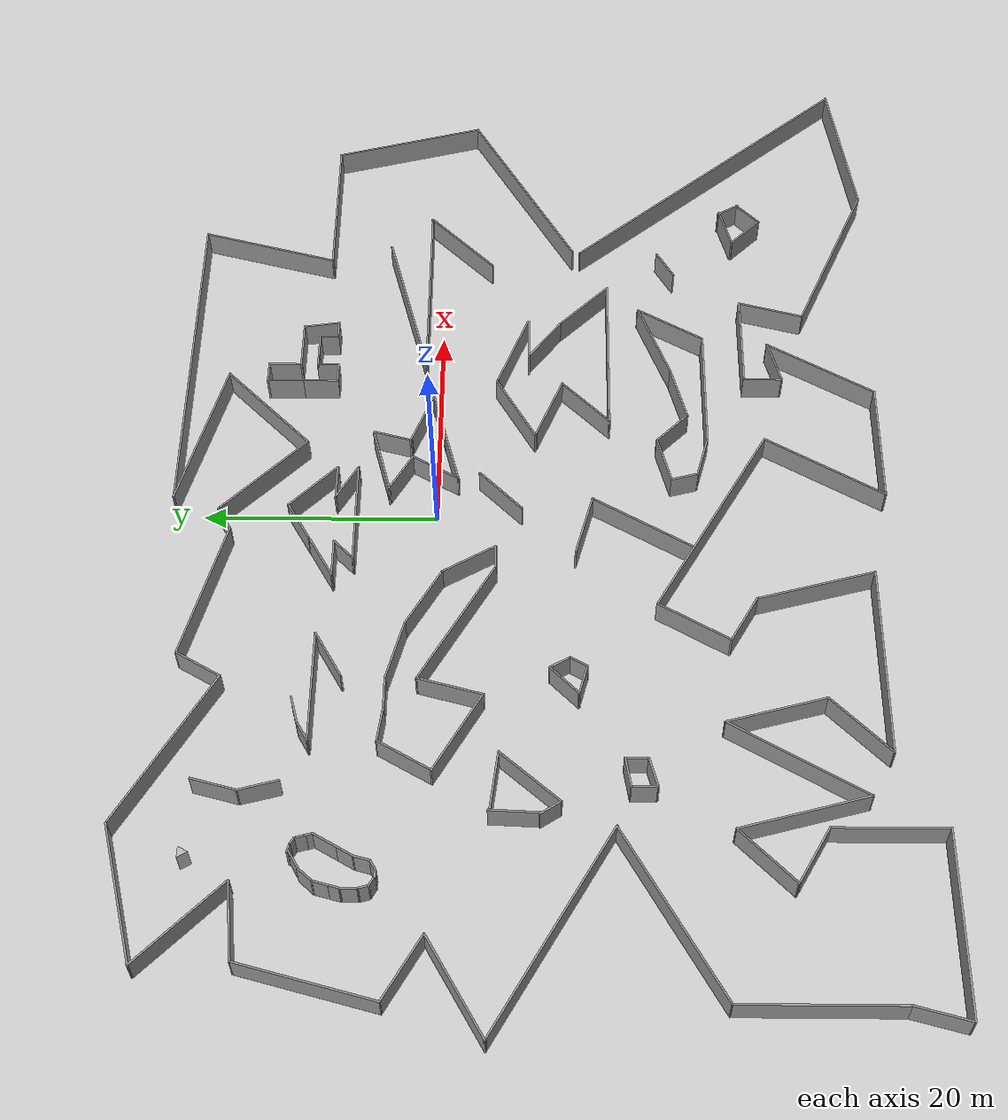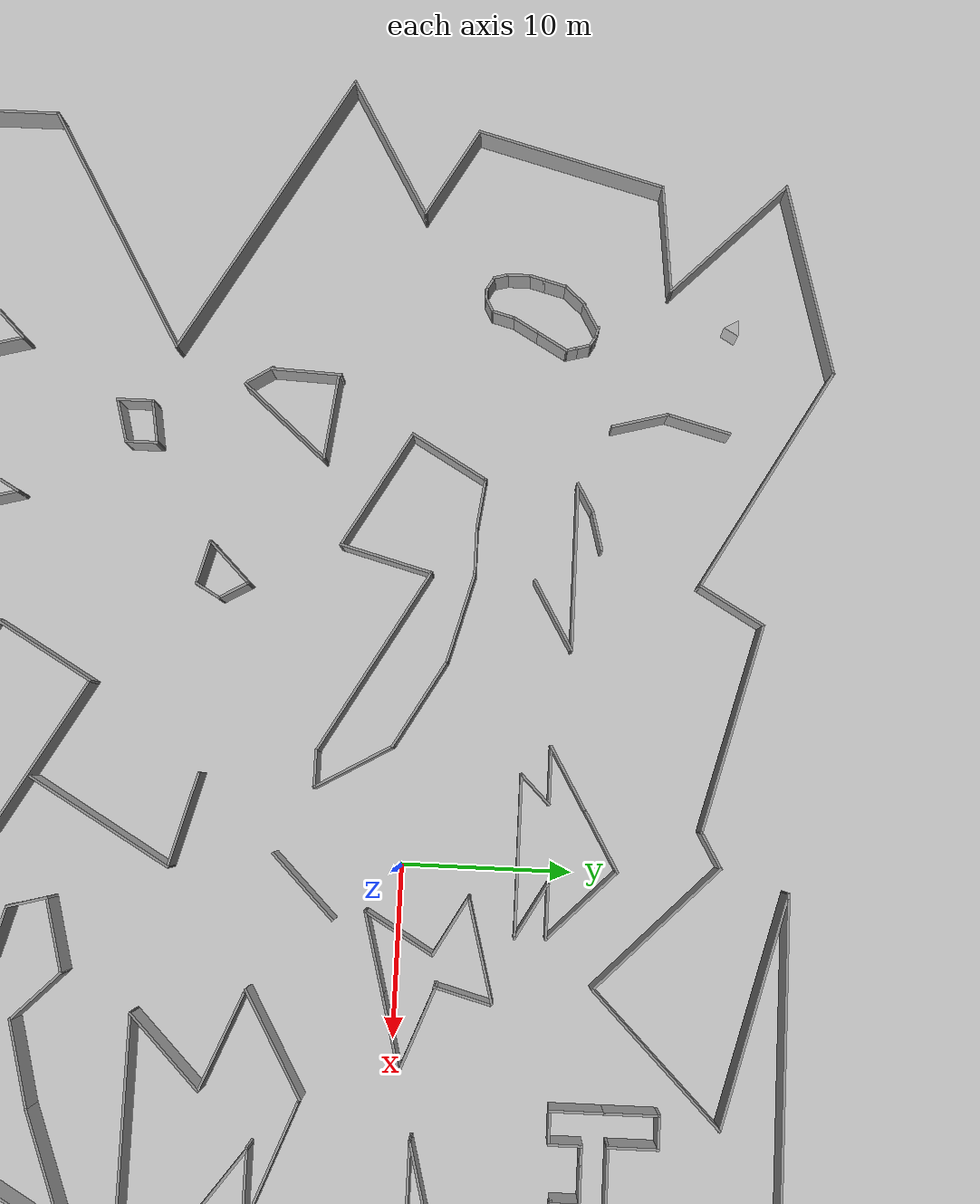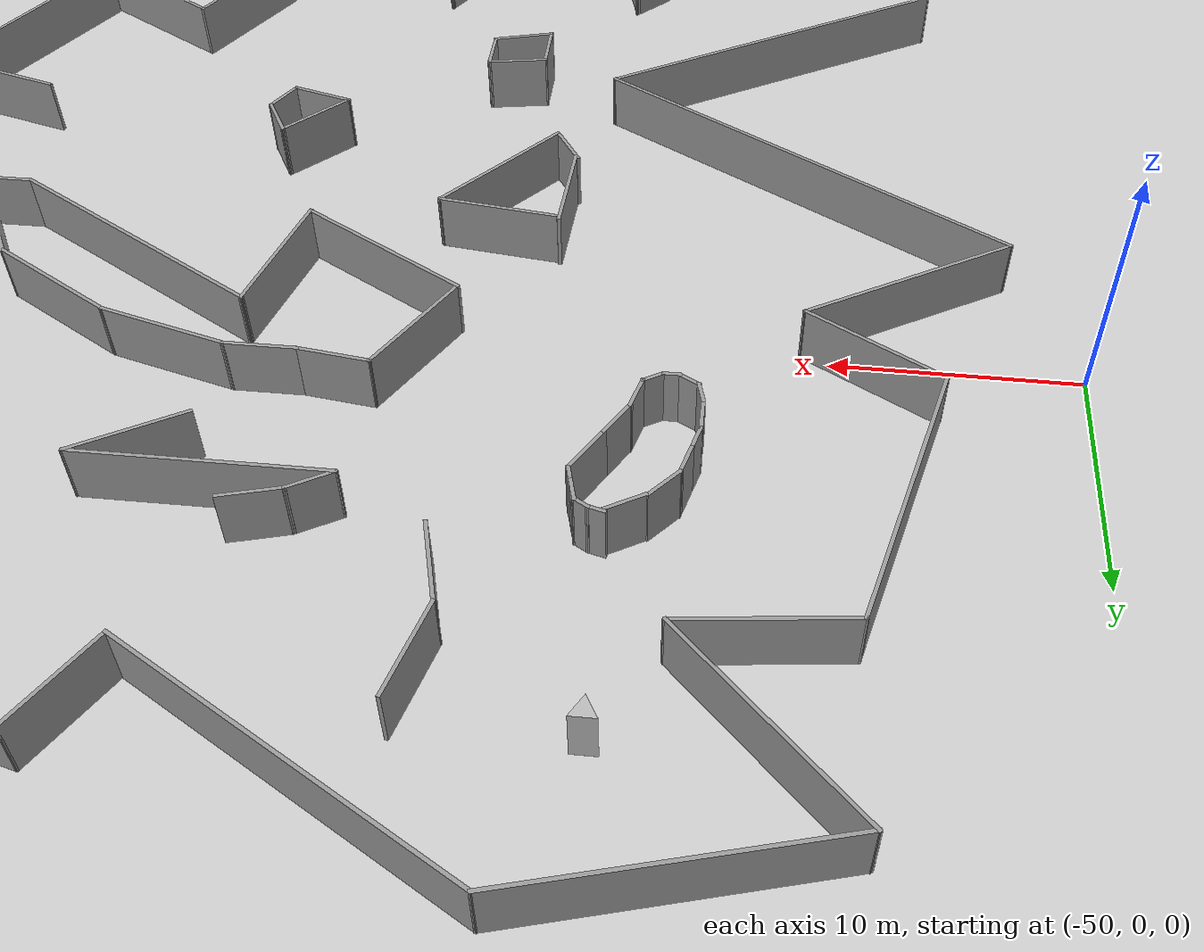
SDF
<sdf version="1.7">
 <world name="default">
  <light name="sun" type="directional">
   <pose>0 0 10 0 -0 0</pose>
   <diffuse>0.8 0.8 0.8 1</diffuse>
   <specular>0.2 0.2 0.2 1</specular>
   <attenuation>
    <range>1000</range>
    <constant>0.9</constant>
    <linear>0.01</linear>
    <quadratic>0.001</quadratic>
   </attenuation>
   <direction>-0.5 0.1 -0.9</direction>
   <spot><inner_angle>0</inner_angle><outer_angle>0</outer_angle><falloff>0</falloff></spot>
  </light>
  <model name="ground_plane">
   <static>1</static>
   <link name="link">
    <collision name="collision">
     <geometry><plane><normal>0 0 1</normal><size>100 100</size></plane></geometry>
     <surface><friction><ode><mu>100</mu><mu2>50</mu2></ode></friction></surface>
    </collision>
    <visual name="visual">
     <cast_shadows>0</cast_shadows>
     <geometry><plane><normal>0 0 1</normal><size>100 100</size></plane></geometry>
     <material>
      <script><uri>file://media/materials/scripts/gazebo.material</uri><name>Gazebo/Grey</name></script>
     </material>
    </visual>
   </link>
  </model>
  <gravity>0 0 -9.8</gravity>
  <magnetic_field>6e-06 2.3e-05 -4.2e-05</magnetic_field>
  <atmosphere type="adiabatic"/>
  <physics type="ode">
   <max_step_size>0.001</max_step_size>
   <real_time_factor>1</real_time_factor>
   <real_time_update_rate>1000</real_time_update_rate>
  </physics>
  <scene><ambient>0.4 0.4 0.4 1</ambient><background>0.7 0.7 0.7 1</background><shadows>1</shadows></scene>
  <audio><device>default</device></audio>
  <spherical_coordinates>
   <surface_model>EARTH_WGS84</surface_model>
   <latitude_deg>0</latitude_deg>
   <longitude_deg>0</longitude_deg>
   <elevation>0</elevation>
   <heading_deg>0</heading_deg>
  </spherical_coordinates>
  <model name="custommap6">
   <pose>1.12082 -8.1027 0 0 -0 0</pose>
   <link name="Wall_0">
    <collision name="Wall_0_Collision">
     <geometry><box><size>11.75 0.15 2.5</size></box></geometry>
     <pose>0 0 1.25 0 -0 0</pose>
    </collision>
    <visual name="Wall_0_Visual">
     <pose>0 0 1.25 0 -0 0</pose>
     <geometry><box><size>11.75 0.15 2.5</size></box></geometry>
     <material>
      <script><uri>file://media/materials/scripts/gazebo.material</uri><name>Gazebo/Grey</name></script>
      <ambient>1 1 1 1</ambient>
     </material>
     <meta><layer>0</layer></meta>
    </visual>
    <pose>-43.8325 16.3365 0 0 -0 -1.8326</pose>
   </link>
   <link name="Wall_1">
    <collision name="Wall_1_Collision">
     <geometry><box><size>6.25 0.15 2.5</size></box></geometry>
     <pose>0 0 1.25 0 -0 0</pose>
    </collision>
    <visual name="Wall_1_Visual">
     <pose>0 0 1.25 0 -0 0</pose>
     <geometry><box><size>6.25 0.15 2.5</size></box></geometry>
     <material>
      <script><uri>file://media/materials/scripts/gazebo.material</uri><name>Gazebo/Grey</name></script>
      <ambient>1 1 1 1</ambient>
     </material>
     <meta><layer>0</layer></meta>
    </visual>
    <pose>-42.6923 9.20912 0 0 -0 -0.523599</pose>
   </link>
   <link name="Wall_10">
    <collision name="Wall_10_Collision">
     <geometry><box><size>6.5 0.15 2.5</size></box></geometry>
     <pose>0 0 1.25 0 -0 0</pose>
    </collision>
    <visual name="Wall_10_Visual">
     <pose>0 0 1.25 0 -0 0</pose>
     <geometry><box><size>6.5 0.15 2.5</size></box></geometry>
     <material>
      <script><uri>file://media/materials/scripts/gazebo.material</uri><name>Gazebo/Grey</name></script>
      <ambient>1 1 1 1</ambient>
     </material>
     <meta><layer>0</layer></meta>
    </visual>
    <pose>-33.5624 -18.2391 0 0 -0 0.785398</pose>
   </link>
   <link name="Wall_100">
    <collision name="Wall_100_Collision">
     <geometry><box><size>4.2808 0.15 2.5</size></box></geometry>
     <pose>0 0 1.25 0 -0 0</pose>
    </collision>
    <visual name="Wall_100_Visual">
     <pose>0 0 1.25 0 -0 0</pose>
     <geometry><box><size>4.2808 0.15 2.5</size></box></geometry>
     <material>
      <script><uri>file://media/materials/scripts/gazebo.material</uri><name>Gazebo/Grey</name></script>
      <ambient>1 1 1 1</ambient>
     </material>
     <meta><layer>0</layer></meta>
    </visual>
    <pose>-29.9794 1.06037 0 0 -0 -1.61612</pose>
   </link>
   <link name="Wall_101">
    <collision name="Wall_101_Collision">
     <geometry><box><size>1.95484 0.15 2.5</size></box></geometry>
     <pose>0 0 1.25 0 -0 0</pose>
    </collision>
    <visual name="Wall_101_Visual">
     <pose>0 0 1.25 0 -0 0</pose>
     <geometry><box><size>1.95484 0.15 2.5</size></box></geometry>
     <material>
      <script><uri>file://media/materials/scripts/gazebo.material</uri><name>Gazebo/Grey</name></script>
      <ambient>1 1 1 1</ambient>
     </material>
     <meta><layer>0</layer></meta>
    </visual>
    <pose>-29.6783 -1.66827 0 0 -0 -0.999139</pose>
   </link>
   <link name="Wall_102">
    <collision name="Wall_102_Collision">
     <geometry><box><size>6.66101 0.15 2.5</size></box></geometry>
     <pose>0 0 1.25 0 -0 0</pose>
    </collision>
    <visual name="Wall_102_Visual">
     <pose>0 0 1.25 0 -0 0</pose>
     <geometry><box><size>6.66101 0.15 2.5</size></box></geometry>
     <material>
      <script><uri>file://media/materials/scripts/gazebo.material</uri><name>Gazebo/Grey</name></script>
      <ambient>1 1 1 1</ambient>
     </material>
     <meta><layer>0</layer></meta>
    </visual>
    <pose>-26.9643 -0.060719 0 0 -0 0.856667</pose>
   </link>
   <link name="Wall_104">
    <collision name="Wall_104_Collision">
     <geometry><box><size>5.07582 0.15 2.5</size></box></geometry>
     <pose>0 0 1.25 0 -0 0</pose>
    </collision>
    <visual name="Wall_104_Visual">
     <pose>0 0 1.25 0 -0 0</pose>
     <geometry><box><size>5.07582 0.15 2.5</size></box></geometry>
     <material>
      <script><uri>file://media/materials/scripts/gazebo.material</uri><name>Gazebo/Grey</name></script>
      <ambient>1 1 1 1</ambient>
     </material>
     <meta><layer>0</layer></meta>
    </visual>
    <pose>-27.2767 2.69877 0 0 -0 -0.121876</pose>
   </link>
   <link name="Wall_107">
    <collision name="Wall_107_Collision">
     <geometry><box><size>6.25 0.15 2.5</size></box></geometry>
     <pose>0 0 1.25 0 -0 0</pose>
    </collision>
    <visual name="Wall_107_Visual">
     <pose>0 0 1.25 0 -0 0</pose>
     <geometry><box><size>6.25 0.15 2.5</size></box></geometry>
     <material>
      <script><uri>file://media/materials/scripts/gazebo.material</uri><name>Gazebo/Grey</name></script>
      <ambient>1 1 1 1</ambient>
     </material>
     <meta><layer>0</layer></meta>
    </visual>
    <pose>3.45301 12.9701 0 0 -0 -2.87979</pose>
   </link>
   <link name="Wall_108">
    <collision name="Wall_108_Collision">
     <geometry><box><size>4 0.15 2.5</size></box></geometry>
     <pose>0 0 1.25 0 -0 0</pose>
    </collision>
    <visual name="Wall_108_Visual">
     <pose>0 0 1.25 0 -0 0</pose>
     <geometry><box><size>4 0.15 2.5</size></box></geometry>
     <material>
      <script><uri>file://media/materials/scripts/gazebo.material</uri><name>Gazebo/Grey</name></script>
      <ambient>1 1 1 1</ambient>
     </material>
     <meta><layer>0</layer></meta>
    </visual>
    <pose>2.17403 11.2182 0 0 -0 -0.523599</pose>
   </link>
   <link name="Wall_109">
    <collision name="Wall_109_Collision">
     <geometry><box><size>4.75 0.15 2.5</size></box></geometry>
     <pose>0 0 1.25 0 -0 0</pose>
    </collision>
    <visual name="Wall_109_Visual">
     <pose>0 0 1.25 0 -0 0</pose>
     <geometry><box><size>4.75 0.15 2.5</size></box></geometry>
     <material>
      <script><uri>file://media/materials/scripts/gazebo.material</uri><name>Gazebo/Grey</name></script>
      <ambient>1 1 1 1</ambient>
     </material>
     <meta><layer>0</layer></meta>
    </visual>
    <pose>2.69113 8.26381 0 0 -0 -2.0944</pose>
   </link>
   <link name="Wall_11">
    <collision name="Wall_11_Collision">
     <geometry><box><size>11.25 0.15 2.5</size></box></geometry>
     <pose>0 0 1.25 0 -0 0</pose>
    </collision>
    <visual name="Wall_11_Visual">
     <pose>0 0 1.25 0 -0 0</pose>
     <geometry><box><size>11.25 0.15 2.5</size></box></geometry>
     <material>
      <script><uri>file://media/materials/scripts/gazebo.material</uri><name>Gazebo/Grey</name></script>
      <ambient>1 1 1 1</ambient>
     </material>
     <meta><layer>0</layer></meta>
    </visual>
    <pose>-29.8809 -21.3549 0 0 -0 -1.309</pose>
   </link>
   <link name="Wall_110">
    <collision name="Wall_110_Collision">
     <geometry><box><size>5 0.15 2.5</size></box></geometry>
     <pose>0 0 1.25 0 -0 0</pose>
    </collision>
    <visual name="Wall_110_Visual">
     <pose>0 0 1.25 0 -0 0</pose>
     <geometry><box><size>5 0.15 2.5</size></box></geometry>
     <material>
      <script><uri>file://media/materials/scripts/gazebo.material</uri><name>Gazebo/Grey</name></script>
      <ambient>1 1 1 1</ambient>
     </material>
     <meta><layer>0</layer></meta>
    </visual>
    <pose>3.8835 6.89959 0 0 -0 0.261799</pose>
   </link>
   <link name="Wall_111">
    <collision name="Wall_111_Collision">
     <geometry><box><size>4.5 0.15 2.5</size></box></geometry>
     <pose>0 0 1.25 0 -0 0</pose>
    </collision>
    <visual name="Wall_111_Visual">
     <pose>0 0 1.25 0 -0 0</pose>
     <geometry><box><size>4.5 0.15 2.5</size></box></geometry>
     <material>
      <script><uri>file://media/materials/scripts/gazebo.material</uri><name>Gazebo/Grey</name></script>
      <ambient>1 1 1 1</ambient>
     </material>
     <meta><layer>0</layer></meta>
    </visual>
    <pose>8.32676 8.09016 0 0 -0 0.261799</pose>
   </link>
   <link name="Wall_112">
    <collision name="Wall_112_Collision">
     <geometry><box><size>5.33597 0.15 2.5</size></box></geometry>
     <pose>0 0 1.25 0 -0 0</pose>
    </collision>
    <visual name="Wall_112_Visual">
     <pose>0 0 1.25 0 -0 0</pose>
     <geometry><box><size>5.33597 0.15 2.5</size></box></geometry>
     <material>
      <script><uri>file://media/materials/scripts/gazebo.material</uri><name>Gazebo/Grey</name></script>
      <ambient>1 1 1 1</ambient>
     </material>
     <meta><layer>0</layer></meta>
    </visual>
    <pose>8.01133 9.5938 0 0 -0 2.77033</pose>
   </link>
   <link name="Wall_113">
    <collision name="Wall_113_Collision">
     <geometry><box><size>3.5 0.15 2.5</size></box></geometry>
     <pose>0 0 1.25 0 -0 0</pose>
    </collision>
    <visual name="Wall_113_Visual">
     <pose>0 0 1.25 0 -0 0</pose>
     <geometry><box><size>3.5 0.15 2.5</size></box></geometry>
     <material>
      <script><uri>file://media/materials/scripts/gazebo.material</uri><name>Gazebo/Grey</name></script>
      <ambient>1 1 1 1</ambient>
     </material>
     <meta><layer>0</layer></meta>
    </visual>
    <pose>6.02853 12.0589 0 0 -0 1.309</pose>
   </link>
   <link name="Wall_115">
    <collision name="Wall_115_Collision">
     <geometry><box><size>9.75 0.15 2.5</size></box></geometry>
     <pose>0 0 1.25 0 -0 0</pose>
    </collision>
    <visual name="Wall_115_Visual">
     <pose>0 0 1.25 0 -0 0</pose>
     <geometry><box><size>9.75 0.15 2.5</size></box></geometry>
     <material>
      <script><uri>file://media/materials/scripts/gazebo.material</uri><name>Gazebo/Grey</name></script>
      <ambient>1 1 1 1</ambient>
     </material>
     <meta><layer>0</layer></meta>
    </visual>
    <pose>-2.89794 -9.40787 0 0 -0 1.0472</pose>
   </link>
   <link name="Wall_116">
    <collision name="Wall_116_Collision">
     <geometry><box><size>5.75 0.15 2.5</size></box></geometry>
     <pose>0 0 1.25 0 -0 0</pose>
    </collision>
    <visual name="Wall_116_Visual">
     <pose>0 0 1.25 0 -0 0</pose>
     <geometry><box><size>5.75 0.15 2.5</size></box></geometry>
     <material>
      <script><uri>file://media/materials/scripts/gazebo.material</uri><name>Gazebo/Grey</name></script>
      <ambient>1 1 1 1</ambient>
     </material>
     <meta><layer>0</layer></meta>
    </visual>
    <pose>-3.20254 -4.52625 0 0 -0 2.87979</pose>
   </link>
   <link name="Wall_118">
    <collision name="Wall_118_Collision">
     <geometry><box><size>5.25 0.15 2.5</size></box></geometry>
     <pose>0 0 1.25 0 -0 0</pose>
    </collision>
    <visual name="Wall_118_Visual">
     <pose>0 0 1.25 0 -0 0</pose>
     <geometry><box><size>5.25 0.15 2.5</size></box></geometry>
     <material>
      <script><uri>file://media/materials/scripts/gazebo.material</uri><name>Gazebo/Grey</name></script>
      <ambient>1 1 1 1</ambient>
     </material>
     <meta><layer>0</layer></meta>
    </visual>
    <pose>0.291453 2.59872 0 0 -0 -2.35619</pose>
   </link>
   <link name="Wall_12">
    <collision name="Wall_12_Collision">
     <geometry><box><size>13 0.15 2.5</size></box></geometry>
     <pose>0 0 1.25 0 -0 0</pose>
    </collision>
    <visual name="Wall_12_Visual">
     <pose>0 0 1.25 0 -0 0</pose>
     <geometry><box><size>13 0.15 2.5</size></box></geometry>
     <material>
      <script><uri>file://media/materials/scripts/gazebo.material</uri><name>Gazebo/Grey</name></script>
      <ambient>1 1 1 1</ambient>
     </material>
     <meta><layer>0</layer></meta>
    </visual>
    <pose>-25.232 -21.1516 0 0 -0 1.0472</pose>
   </link>
   <link name="Wall_120">
    <collision name="Wall_120_Collision">
     <geometry><box><size>14.5 0.15 2.5</size></box></geometry>
     <pose>0 0 1.25 0 -0 0</pose>
    </collision>
    <visual name="Wall_120_Visual">
     <pose>0 0 1.25 0 -0 0</pose>
     <geometry><box><size>14.5 0.15 2.5</size></box></geometry>
     <material>
      <script><uri>file://media/materials/scripts/gazebo.material</uri><name>Gazebo/Grey</name></script>
      <ambient>1 1 1 1</ambient>
     </material>
     <meta><layer>0</layer></meta>
    </visual>
    <pose>21.1782 11.341 0 0 -0 -2.87979</pose>
   </link>
   <link name="Wall_121">
    <collision name="Wall_121_Collision">
     <geometry><box><size>17.5 0.15 2.5</size></box></geometry>
     <pose>0 0 1.25 0 -0 0</pose>
    </collision>
    <visual name="Wall_121_Visual">
     <pose>0 0 1.25 0 -0 0</pose>
     <geometry><box><size>17.5 0.15 2.5</size></box></geometry>
     <material>
      <script><uri>file://media/materials/scripts/gazebo.material</uri><name>Gazebo/Grey</name></script>
      <ambient>1 1 1 1</ambient>
     </material>
     <meta><layer>0</layer></meta>
    </visual>
    <pose>22.9227 9.48395 0 0 -0 0</pose>
   </link>
   <link name="Wall_122">
    <collision name="Wall_122_Collision">
     <geometry><box><size>8.25 0.15 2.5</size></box></geometry>
     <pose>0 0 1.25 0 -0 0</pose>
    </collision>
    <visual name="Wall_122_Visual">
     <pose>0 0 1.25 0 -0 0</pose>
     <geometry><box><size>8.25 0.15 2.5</size></box></geometry>
     <material>
      <script><uri>file://media/materials/scripts/gazebo.material</uri><name>Gazebo/Grey</name></script>
      <ambient>1 1 1 1</ambient>
     </material>
     <meta><layer>0</layer></meta>
    </visual>
    <pose>28.7339 6.62017 0 0 -0 -2.35619</pose>
   </link>
   <link name="Wall_124">
    <collision name="Wall_124_Collision">
     <geometry><box><size>4.25 0.15 2.5</size></box></geometry>
     <pose>0 0 1.25 0 -0 0</pose>
    </collision>
    <visual name="Wall_124_Visual">
     <pose>0 0 1.25 0 -0 0</pose>
     <geometry><box><size>4.25 0.15 2.5</size></box></geometry>
     <material>
      <script><uri>file://media/materials/scripts/gazebo.material</uri><name>Gazebo/Grey</name></script>
      <ambient>1 1 1 1</ambient>
     </material>
     <meta><layer>0</layer></meta>
    </visual>
    <pose>-6.60542 17.6004 0 0 -0 -2.61799</pose>
   </link>
   <link name="Wall_125">
    <collision name="Wall_125_Collision">
     <geometry><box><size>3.5 0.15 2.5</size></box></geometry>
     <pose>0 0 1.25 0 -0 0</pose>
    </collision>
    <visual name="Wall_125_Visual">
     <pose>0 0 1.25 0 -0 0</pose>
     <geometry><box><size>3.5 0.15 2.5</size></box></geometry>
     <material>
      <script><uri>file://media/materials/scripts/gazebo.material</uri><name>Gazebo/Grey</name></script>
      <ambient>1 1 1 1</ambient>
     </material>
     <meta><layer>0</layer></meta>
    </visual>
    <pose>-6.70577 16.5754 0 0 -0 0</pose>
   </link>
   <link name="Wall_126">
    <collision name="Wall_126_Collision">
     <geometry><box><size>2.5 0.15 2.5</size></box></geometry>
     <pose>0 0 1.25 0 -0 0</pose>
    </collision>
    <visual name="Wall_126_Visual">
     <pose>0 0 1.25 0 -0 0</pose>
     <geometry><box><size>2.5 0.15 2.5</size></box></geometry>
     <material>
      <script><uri>file://media/materials/scripts/gazebo.material</uri><name>Gazebo/Grey</name></script>
      <ambient>1 1 1 1</ambient>
     </material>
     <meta><layer>0</layer></meta>
    </visual>
    <pose>-5.86162 15.7446 0 0 -0 -2.35619</pose>
   </link>
   <link name="Wall_127">
    <collision name="Wall_127_Collision">
     <geometry><box><size>9.5 0.15 2.5</size></box></geometry>
     <pose>0 0 1.25 0 -0 0</pose>
    </collision>
    <visual name="Wall_127_Visual">
     <pose>0 0 1.25 0 -0 0</pose>
     <geometry><box><size>9.5 0.15 2.5</size></box></geometry>
     <material>
      <script><uri>file://media/materials/scripts/gazebo.material</uri><name>Gazebo/Grey</name></script>
      <ambient>1 1 1 1</ambient>
     </material>
     <meta><layer>0</layer></meta>
    </visual>
    <pose>-2.01747 14.9137 0 0 -0 0</pose>
   </link>
   <link name="Wall_128">
    <collision name="Wall_128_Collision">
     <geometry><box><size>3.75 0.15 2.5</size></box></geometry>
     <pose>0 0 1.25 0 -0 0</pose>
    </collision>
    <visual name="Wall_128_Visual">
     <pose>0 0 1.25 0 -0 0</pose>
     <geometry><box><size>3.75 0.15 2.5</size></box></geometry>
     <material>
      <script><uri>file://media/materials/scripts/gazebo.material</uri><name>Gazebo/Grey</name></script>
      <ambient>1 1 1 1</ambient>
     </material>
     <meta><layer>0</layer></meta>
    </visual>
    <pose>1.09868 15.8137 0 0 -0 2.61799</pose>
   </link>
   <link name="Wall_129">
    <collision name="Wall_129_Collision">
     <geometry><box><size>3.25 0.15 2.5</size></box></geometry>
     <pose>0 0 1.25 0 -0 0</pose>
    </collision>
    <visual name="Wall_129_Visual">
     <pose>0 0 1.25 0 -0 0</pose>
     <geometry><box><size>3.25 0.15 2.5</size></box></geometry>
     <material>
      <script><uri>file://media/materials/scripts/gazebo.material</uri><name>Gazebo/Grey</name></script>
      <ambient>1 1 1 1</ambient>
     </material>
     <meta><layer>0</layer></meta>
    </visual>
    <pose>1.08984 16.7137 0 0 -0 0</pose>
   </link>
   <link name="Wall_13">
    <collision name="Wall_13_Collision">
     <geometry><box><size>8.75 0.15 2.5</size></box></geometry>
     <pose>0 0 1.25 0 -0 0</pose>
    </collision>
    <visual name="Wall_13_Visual">
     <pose>0 0 1.25 0 -0 0</pose>
     <geometry><box><size>8.75 0.15 2.5</size></box></geometry>
     <material>
      <script><uri>file://media/materials/scripts/gazebo.material</uri><name>Gazebo/Grey</name></script>
      <ambient>1 1 1 1</ambient>
     </material>
     <meta><layer>0</layer></meta>
    </visual>
    <pose>-20.9066 -19.7408 0 0 -0 -1.309</pose>
   </link>
   <link name="Wall_130">
    <collision name="Wall_130_Collision">
     <geometry><box><size>5.75 0.15 2.5</size></box></geometry>
     <pose>0 0 1.25 0 -0 0</pose>
    </collision>
    <visual name="Wall_130_Visual">
     <pose>0 0 1.25 0 -0 0</pose>
     <geometry><box><size>5.75 0.15 2.5</size></box></geometry>
     <material>
      <script><uri>file://media/materials/scripts/gazebo.material</uri><name>Gazebo/Grey</name></script>
      <ambient>1 1 1 1</ambient>
     </material>
     <meta><layer>0</layer></meta>
    </visual>
    <pose>0.65994 18.6936 0 0 -0 2.35619</pose>
   </link>
   <link name="Wall_131">
    <collision name="Wall_131_Collision">
     <geometry><box><size>4 0.15 2.5</size></box></geometry>
     <pose>0 0 1.25 0 -0 0</pose>
    </collision>
    <visual name="Wall_131_Visual">
     <pose>0 0 1.25 0 -0 0</pose>
     <geometry><box><size>4 0.15 2.5</size></box></geometry>
     <material>
      <script><uri>file://media/materials/scripts/gazebo.material</uri><name>Gazebo/Grey</name></script>
      <ambient>1 1 1 1</ambient>
     </material>
     <meta><layer>0</layer></meta>
    </visual>
    <pose>-2.98706 19.711 0 0 -0 -2.61799</pose>
   </link>
   <link name="Wall_133">
    <collision name="Wall_133_Collision">
     <geometry><box><size>4.5 0.15 2.5</size></box></geometry>
     <pose>0 0 1.25 0 -0 0</pose>
    </collision>
    <visual name="Wall_133_Visual">
     <pose>0 0 1.25 0 -0 0</pose>
     <geometry><box><size>4.5 0.15 2.5</size></box></geometry>
     <material>
      <script><uri>file://media/materials/scripts/gazebo.material</uri><name>Gazebo/Grey</name></script>
      <ambient>1 1 1 1</ambient>
     </material>
     <meta><layer>0</layer></meta>
    </visual>
    <pose>16.2018 20.6841 0 0 -0 3.14159</pose>
   </link>
   <link name="Wall_134">
    <collision name="Wall_134_Collision">
     <geometry><box><size>3 0.15 2.5</size></box></geometry>
     <pose>0 0 1.25 0 -0 0</pose>
    </collision>
    <visual name="Wall_134_Visual">
     <pose>0 0 1.25 0 -0 0</pose>
     <geometry><box><size>3 0.15 2.5</size></box></geometry>
     <material>
      <script><uri>file://media/materials/scripts/gazebo.material</uri><name>Gazebo/Grey</name></script>
      <ambient>1 1 1 1</ambient>
     </material>
     <meta><layer>0</layer></meta>
    </visual>
    <pose>14.0268 22.1091 0 0 -0 1.5708</pose>
   </link>
   <link name="Wall_135">
    <collision name="Wall_135_Collision">
     <geometry><box><size>2 0.15 2.5</size></box></geometry>
     <pose>0 0 1.25 0 -0 0</pose>
    </collision>
    <visual name="Wall_135_Visual">
     <pose>0 0 1.25 0 -0 0</pose>
     <geometry><box><size>2 0.15 2.5</size></box></geometry>
     <material>
      <script><uri>file://media/materials/scripts/gazebo.material</uri><name>Gazebo/Grey</name></script>
      <ambient>1 1 1 1</ambient>
     </material>
     <meta><layer>0</layer></meta>
    </visual>
    <pose>13.1018 23.5341 0 0 -0 3.14159</pose>
   </link>
   <link name="Wall_136">
    <collision name="Wall_136_Collision">
     <geometry><box><size>3.25 0.15 2.5</size></box></geometry>
     <pose>0 0 1.25 0 -0 0</pose>
    </collision>
    <visual name="Wall_136_Visual">
     <pose>0 0 1.25 0 -0 0</pose>
     <geometry><box><size>3.25 0.15 2.5</size></box></geometry>
     <material>
      <script><uri>file://media/materials/scripts/gazebo.material</uri><name>Gazebo/Grey</name></script>
      <ambient>1 1 1 1</ambient>
     </material>
     <meta><layer>0</layer></meta>
    </visual>
    <pose>12.1768 21.9841 0 0 -0 -1.5708</pose>
   </link>
   <link name="Wall_137">
    <collision name="Wall_137_Collision">
     <geometry><box><size>3.25 0.15 2.5</size></box></geometry>
     <pose>0 0 1.25 0 -0 0</pose>
    </collision>
    <visual name="Wall_137_Visual">
     <pose>0 0 1.25 0 -0 0</pose>
     <geometry><box><size>3.25 0.15 2.5</size></box></geometry>
     <material>
      <script><uri>file://media/materials/scripts/gazebo.material</uri><name>Gazebo/Grey</name></script>
      <ambient>1 1 1 1</ambient>
     </material>
     <meta><layer>0</layer></meta>
    </visual>
    <pose>12.1768 18.8841 0 0 -0 -1.5708</pose>
   </link>
   <link name="Wall_138">
    <collision name="Wall_138_Collision">
     <geometry><box><size>2 0.15 2.5</size></box></geometry>
     <pose>0 0 1.25 0 -0 0</pose>
    </collision>
    <visual name="Wall_138_Visual">
     <pose>0 0 1.25 0 -0 0</pose>
     <geometry><box><size>2 0.15 2.5</size></box></geometry>
     <material>
      <script><uri>file://media/materials/scripts/gazebo.material</uri><name>Gazebo/Grey</name></script>
      <ambient>1 1 1 1</ambient>
     </material>
     <meta><layer>0</layer></meta>
    </visual>
    <pose>13.1018 17.3341 0 0 -0 0</pose>
   </link>
   <link name="Wall_139">
    <collision name="Wall_139_Collision">
     <geometry><box><size>2 0.15 2.5</size></box></geometry>
     <pose>0 0 1.25 0 -0 0</pose>
    </collision>
    <visual name="Wall_139_Visual">
     <pose>0 0 1.25 0 -0 0</pose>
     <geometry><box><size>2 0.15 2.5</size></box></geometry>
     <material>
      <script><uri>file://media/materials/scripts/gazebo.material</uri><name>Gazebo/Grey</name></script>
      <ambient>1 1 1 1</ambient>
     </material>
     <meta><layer>0</layer></meta>
    </visual>
    <pose>14.0268 18.2591 0 0 -0 1.5708</pose>
   </link>
   <link name="Wall_14">
    <collision name="Wall_14_Collision">
     <geometry><box><size>7 0.15 2.5</size></box></geometry>
     <pose>0 0 1.25 0 -0 0</pose>
    </collision>
    <visual name="Wall_14_Visual">
     <pose>0 0 1.25 0 -0 0</pose>
     <geometry><box><size>7 0.15 2.5</size></box></geometry>
     <material>
      <script><uri>file://media/materials/scripts/gazebo.material</uri><name>Gazebo/Grey</name></script>
      <ambient>1 1 1 1</ambient>
     </material>
     <meta><layer>0</layer></meta>
    </visual>
    <pose>-22.2155 -26.3162 0 0 -0 -2.35619</pose>
   </link>
   <link name="Wall_140">
    <collision name="Wall_140_Collision">
     <geometry><box><size>1.25 0.15 2.5</size></box></geometry>
     <pose>0 0 1.25 0 -0 0</pose>
    </collision>
    <visual name="Wall_140_Visual">
     <pose>0 0 1.25 0 -0 0</pose>
     <geometry><box><size>1.25 0.15 2.5</size></box></geometry>
     <material>
      <script><uri>file://media/materials/scripts/gazebo.material</uri><name>Gazebo/Grey</name></script>
      <ambient>1 1 1 1</ambient>
     </material>
     <meta><layer>0</layer></meta>
    </visual>
    <pose>14.5768 19.1841 0 0 -0 0</pose>
   </link>
   <link name="Wall_141">
    <collision name="Wall_141_Collision">
     <geometry><box><size>2.25 0.15 2.5</size></box></geometry>
     <pose>0 0 1.25 0 -0 0</pose>
    </collision>
    <visual name="Wall_141_Visual">
     <pose>0 0 1.25 0 -0 0</pose>
     <geometry><box><size>2.25 0.15 2.5</size></box></geometry>
     <material>
      <script><uri>file://media/materials/scripts/gazebo.material</uri><name>Gazebo/Grey</name></script>
      <ambient>1 1 1 1</ambient>
     </material>
     <meta><layer>0</layer></meta>
    </visual>
    <pose>16.1768 19.1841 0 0 -0 0</pose>
   </link>
   <link name="Wall_142">
    <collision name="Wall_142_Collision">
     <geometry><box><size>1.75 0.15 2.5</size></box></geometry>
     <pose>0 0 1.25 0 -0 0</pose>
    </collision>
    <visual name="Wall_142_Visual">
     <pose>0 0 1.25 0 -0 0</pose>
     <geometry><box><size>1.75 0.15 2.5</size></box></geometry>
     <material>
      <script><uri>file://media/materials/scripts/gazebo.material</uri><name>Gazebo/Grey</name></script>
      <ambient>1 1 1 1</ambient>
     </material>
     <meta><layer>0</layer></meta>
    </visual>
    <pose>17.2268 18.3841 0 0 -0 -1.5708</pose>
   </link>
   <link name="Wall_143">
    <collision name="Wall_143_Collision">
     <geometry><box><size>1.75 0.15 2.5</size></box></geometry>
     <pose>0 0 1.25 0 -0 0</pose>
    </collision>
    <visual name="Wall_143_Visual">
     <pose>0 0 1.25 0 -0 0</pose>
     <geometry><box><size>1.75 0.15 2.5</size></box></geometry>
     <material>
      <script><uri>file://media/materials/scripts/gazebo.material</uri><name>Gazebo/Grey</name></script>
      <ambient>1 1 1 1</ambient>
     </material>
     <meta><layer>0</layer></meta>
    </visual>
    <pose>18.0268 17.5841 0 0 -0 0</pose>
   </link>
   <link name="Wall_144">
    <collision name="Wall_144_Collision">
     <geometry><box><size>3.28249 0.15 2.5</size></box></geometry>
     <pose>0 0 1.25 0 -0 0</pose>
    </collision>
    <visual name="Wall_144_Visual">
     <pose>0 0 1.25 0 -0 0</pose>
     <geometry><box><size>3.28249 0.15 2.5</size></box></geometry>
     <material>
      <script><uri>file://media/materials/scripts/gazebo.material</uri><name>Gazebo/Grey</name></script>
      <ambient>1 1 1 1</ambient>
     </material>
     <meta><layer>0</layer></meta>
    </visual>
    <pose>18.6018 19.1341 0 0 -0 1.71495</pose>
   </link>
   <link name="Wall_146">
    <collision name="Wall_146_Collision">
     <geometry><box><size>5.25 0.15 2.5</size></box></geometry>
     <pose>0 0 1.25 0 -0 0</pose>
    </collision>
    <visual name="Wall_146_Visual">
     <pose>0 0 1.25 0 -0 0</pose>
     <geometry><box><size>5.25 0.15 2.5</size></box></geometry>
     <material>
      <script><uri>file://media/materials/scripts/gazebo.material</uri><name>Gazebo/Grey</name></script>
      <ambient>1 1 1 1</ambient>
     </material>
     <meta><layer>0</layer></meta>
    </visual>
    <pose>10.9542 -13.0083 0 0 -0 -2.87979</pose>
   </link>
   <link name="Wall_147">
    <collision name="Wall_147_Collision">
     <geometry><box><size>4 0.15 2.5</size></box></geometry>
     <pose>0 0 1.25 0 -0 0</pose>
    </collision>
    <visual name="Wall_147_Visual">
     <pose>0 0 1.25 0 -0 0</pose>
     <geometry><box><size>4 0.15 2.5</size></box></geometry>
     <material>
      <script><uri>file://media/materials/scripts/gazebo.material</uri><name>Gazebo/Grey</name></script>
      <ambient>1 1 1 1</ambient>
     </material>
     <meta><layer>0</layer></meta>
    </visual>
    <pose>7.12989 -12.3071 0 0 -0 2.35619</pose>
   </link>
   <link name="Wall_148">
    <collision name="Wall_148_Collision">
     <geometry><box><size>4.5 0.15 2.5</size></box></geometry>
     <pose>0 0 1.25 0 -0 0</pose>
    </collision>
    <visual name="Wall_148_Visual">
     <pose>0 0 1.25 0 -0 0</pose>
     <geometry><box><size>4.5 0.15 2.5</size></box></geometry>
     <material>
      <script><uri>file://media/materials/scripts/gazebo.material</uri><name>Gazebo/Grey</name></script>
      <ambient>1 1 1 1</ambient>
     </material>
     <meta><layer>0</layer></meta>
    </visual>
    <pose>3.66783 -11.5088 0 0 -0 -2.87979</pose>
   </link>
   <link name="Wall_149">
    <collision name="Wall_149_Collision">
     <geometry><box><size>2.5 0.15 2.5</size></box></geometry>
     <pose>0 0 1.25 0 -0 0</pose>
    </collision>
    <visual name="Wall_149_Visual">
     <pose>0 0 1.25 0 -0 0</pose>
     <geometry><box><size>2.5 0.15 2.5</size></box></geometry>
     <material>
      <script><uri>file://media/materials/scripts/gazebo.material</uri><name>Gazebo/Grey</name></script>
      <ambient>1 1 1 1</ambient>
     </material>
     <meta><layer>0</layer></meta>
    </visual>
    <pose>1.87105 -13.2067 0 0 -0 -1.309</pose>
   </link>
   <link name="Wall_15">
    <collision name="Wall_15_Collision">
     <geometry><box><size>17 0.15 2.5</size></box></geometry>
     <pose>0 0 1.25 0 -0 0</pose>
    </collision>
    <visual name="Wall_15_Visual">
     <pose>0 0 1.25 0 -0 0</pose>
     <geometry><box><size>17 0.15 2.5</size></box></geometry>
     <material>
      <script><uri>file://media/materials/scripts/gazebo.material</uri><name>Gazebo/Grey</name></script>
      <ambient>1 1 1 1</ambient>
     </material>
     <meta><layer>0</layer></meta>
    </visual>
    <pose>-16.2123 -28.738 0 0 -0 0</pose>
   </link>
   <link name="Wall_150">
    <collision name="Wall_150_Collision">
     <geometry><box><size>4 0.15 2.5</size></box></geometry>
     <pose>0 0 1.25 0 -0 0</pose>
    </collision>
    <visual name="Wall_150_Visual">
     <pose>0 0 1.25 0 -0 0</pose>
     <geometry><box><size>4 0.15 2.5</size></box></geometry>
     <material>
      <script><uri>file://media/materials/scripts/gazebo.material</uri><name>Gazebo/Grey</name></script>
      <ambient>1 1 1 1</ambient>
     </material>
     <meta><layer>0</layer></meta>
    </visual>
    <pose>4.03457 -14.8399 0 0 -0 -0.261799</pose>
   </link>
   <link name="Wall_151">
    <collision name="Wall_151_Collision">
     <geometry><box><size>11.5 0.15 2.5</size></box></geometry>
     <pose>0 0 1.25 0 -0 0</pose>
    </collision>
    <visual name="Wall_151_Visual">
     <pose>0 0 1.25 0 -0 0</pose>
     <geometry><box><size>11.5 0.15 2.5</size></box></geometry>
     <material>
      <script><uri>file://media/materials/scripts/gazebo.material</uri><name>Gazebo/Grey</name></script>
      <ambient>1 1 1 1</ambient>
     </material>
     <meta><layer>0</layer></meta>
    </visual>
    <pose>11.569 -15.3382 0 0 -0 0</pose>
   </link>
   <link name="Wall_152">
    <collision name="Wall_152_Collision">
     <geometry><box><size>6.75 0.15 2.5</size></box></geometry>
     <pose>0 0 1.25 0 -0 0</pose>
    </collision>
    <visual name="Wall_152_Visual">
     <pose>0 0 1.25 0 -0 0</pose>
     <geometry><box><size>6.75 0.15 2.5</size></box></geometry>
     <material>
      <script><uri>file://media/materials/scripts/gazebo.material</uri><name>Gazebo/Grey</name></script>
      <ambient>1 1 1 1</ambient>
     </material>
     <meta><layer>0</layer></meta>
    </visual>
    <pose>18.894 -12.4803 0 0 -0 1.0472</pose>
   </link>
   <link name="Wall_153">
    <collision name="Wall_153_Collision">
     <geometry><box><size>7.78021 0.15 2.5</size></box></geometry>
     <pose>0 0 1.25 0 -0 0</pose>
    </collision>
    <visual name="Wall_153_Visual">
     <pose>0 0 1.25 0 -0 0</pose>
     <geometry><box><size>7.78021 0.15 2.5</size></box></geometry>
     <material>
      <script><uri>file://media/materials/scripts/gazebo.material</uri><name>Gazebo/Grey</name></script>
      <ambient>1 1 1 1</ambient>
     </material>
     <meta><layer>0</layer></meta>
    </visual>
    <pose>16.9806 -10.9853 0 0 -0 -2.77627</pose>
   </link>
   <link name="Wall_155">
    <collision name="Wall_155_Collision">
     <geometry><box><size>4 0.15 2.5</size></box></geometry>
     <pose>0 0 1.25 0 -0 0</pose>
    </collision>
    <visual name="Wall_155_Visual">
     <pose>0 0 1.25 0 -0 0</pose>
     <geometry><box><size>4 0.15 2.5</size></box></geometry>
     <material>
      <script><uri>file://media/materials/scripts/gazebo.material</uri><name>Gazebo/Grey</name></script>
      <ambient>1 1 1 1</ambient>
     </material>
     <meta><layer>0</layer></meta>
    </visual>
    <pose>30.8646 -18.0666 0 0 -0 -2.87979</pose>
   </link>
   <link name="Wall_156">
    <collision name="Wall_156_Collision">
     <geometry><box><size>3.76094 0.15 2.5</size></box></geometry>
     <pose>0 0 1.25 0 -0 0</pose>
    </collision>
    <visual name="Wall_156_Visual">
     <pose>0 0 1.25 0 -0 0</pose>
     <geometry><box><size>3.76094 0.15 2.5</size></box></geometry>
     <material>
      <script><uri>file://media/materials/scripts/gazebo.material</uri><name>Gazebo/Grey</name></script>
      <ambient>1 1 1 1</ambient>
     </material>
     <meta><layer>0</layer></meta>
    </visual>
    <pose>30.2818 -19.9491 0 0 -0 -0.785398</pose>
   </link>
   <link name="Wall_157">
    <collision name="Wall_157_Collision">
     <geometry><box><size>2.99248 0.15 2.5</size></box></geometry>
     <pose>0 0 1.25 0 -0 0</pose>
    </collision>
    <visual name="Wall_157_Visual">
     <pose>0 0 1.25 0 -0 0</pose>
     <geometry><box><size>2.99248 0.15 2.5</size></box></geometry>
     <material>
      <script><uri>file://media/materials/scripts/gazebo.material</uri><name>Gazebo/Grey</name></script>
      <ambient>1 1 1 1</ambient>
     </material>
     <meta><layer>0</layer></meta>
    </visual>
    <pose>32.578 -20.2355 0 0 -0 0.770832</pose>
   </link>
   <link name="Wall_158">
    <collision name="Wall_158_Collision">
     <geometry><box><size>2.25 0.15 2.5</size></box></geometry>
     <pose>0 0 1.25 0 -0 0</pose>
    </collision>
    <visual name="Wall_158_Visual">
     <pose>0 0 1.25 0 -0 0</pose>
     <geometry><box><size>2.25 0.15 2.5</size></box></geometry>
     <material>
      <script><uri>file://media/materials/scripts/gazebo.material</uri><name>Gazebo/Grey</name></script>
      <ambient>1 1 1 1</ambient>
     </material>
     <meta><layer>0</layer></meta>
    </visual>
    <pose>33.0725 -18.4436 0 0 -0 2.0944</pose>
   </link>
   <link name="Wall_16">
    <collision name="Wall_16_Collision">
     <geometry><box><size>10.5 0.15 2.5</size></box></geometry>
     <pose>0 0 1.25 0 -0 0</pose>
    </collision>
    <visual name="Wall_16_Visual">
     <pose>0 0 1.25 0 -0 0</pose>
     <geometry><box><size>10.5 0.15 2.5</size></box></geometry>
     <material>
      <script><uri>file://media/materials/scripts/gazebo.material</uri><name>Gazebo/Grey</name></script>
      <ambient>1 1 1 1</ambient>
     </material>
     <meta><layer>0</layer></meta>
    </visual>
    <pose>-9.12671 -23.7393 0 0 -0 1.8326</pose>
   </link>
   <link name="Wall_160">
    <collision name="Wall_160_Collision">
     <geometry><box><size>3 0.15 2.5</size></box></geometry>
     <pose>0 0 1.25 0 -0 0</pose>
    </collision>
    <visual name="Wall_160_Visual">
     <pose>0 0 1.25 0 -0 0</pose>
     <geometry><box><size>3 0.15 2.5</size></box></geometry>
     <material>
      <script><uri>file://media/materials/scripts/gazebo.material</uri><name>Gazebo/Grey</name></script>
      <ambient>1 1 1 1</ambient>
     </material>
     <meta><layer>0</layer></meta>
    </visual>
    <pose>26.1093 -12.2546 0 0 -0 -2.61799</pose>
   </link>
   <link name="Wall_162">
    <collision name="Wall_162_Collision">
     <geometry><box><size>4 0.15 2.5</size></box></geometry>
     <pose>0 0 1.25 0 -0 0</pose>
    </collision>
    <visual name="Wall_162_Visual">
     <pose>0 0 1.25 0 -0 0</pose>
     <geometry><box><size>4 0.15 2.5</size></box></geometry>
     <material>
      <script><uri>file://media/materials/scripts/gazebo.material</uri><name>Gazebo/Grey</name></script>
      <ambient>1 1 1 1</ambient>
     </material>
     <meta><layer>0</layer></meta>
    </visual>
    <pose>-27.8334 24.5468 0 0 -0 -1.8326</pose>
   </link>
   <link name="Wall_163">
    <collision name="Wall_163_Collision">
     <geometry><box><size>3.5 0.15 2.5</size></box></geometry>
     <pose>0 0 1.25 0 -0 0</pose>
    </collision>
    <visual name="Wall_163_Visual">
     <pose>0 0 1.25 0 -0 0</pose>
     <geometry><box><size>3.5 0.15 2.5</size></box></geometry>
     <material>
      <script><uri>file://media/materials/scripts/gazebo.material</uri><name>Gazebo/Grey</name></script>
      <ambient>1 1 1 1</ambient>
     </material>
     <meta><layer>0</layer></meta>
    </visual>
    <pose>-27.8981 21.0695 0 0 -0 -1.309</pose>
   </link>
   <link name="Wall_17">
    <collision name="Wall_17_Collision">
     <geometry><box><size>4.75 0.15 2.5</size></box></geometry>
     <pose>0 0 1.25 0 -0 0</pose>
    </collision>
    <visual name="Wall_17_Visual">
     <pose>0 0 1.25 0 -0 0</pose>
     <geometry><box><size>4.75 0.15 2.5</size></box></geometry>
     <material>
      <script><uri>file://media/materials/scripts/gazebo.material</uri><name>Gazebo/Grey</name></script>
      <ambient>1 1 1 1</ambient>
     </material>
     <meta><layer>0</layer></meta>
    </visual>
    <pose>-12.458 -17.5907 0 0 -0 2.61799</pose>
   </link>
   <link name="Wall_18">
    <collision name="Wall_18_Collision">
     <geometry><box><size>7 0.15 2.5</size></box></geometry>
     <pose>0 0 1.25 0 -0 0</pose>
    </collision>
    <visual name="Wall_18_Visual">
     <pose>0 0 1.25 0 -0 0</pose>
     <geometry><box><size>7 0.15 2.5</size></box></geometry>
     <material>
      <script><uri>file://media/materials/scripts/gazebo.material</uri><name>Gazebo/Grey</name></script>
      <ambient>1 1 1 1</ambient>
     </material>
     <meta><layer>0</layer></meta>
    </visual>
    <pose>-12.7373 -13.4745 0 0 -0 1.0472</pose>
   </link>
   <link name="Wall_19">
    <collision name="Wall_19_Collision">
     <geometry><box><size>19.75 0.15 2.5</size></box></geometry>
     <pose>0 0 1.25 0 -0 0</pose>
    </collision>
    <visual name="Wall_19_Visual">
     <pose>0 0 1.25 0 -0 0</pose>
     <geometry><box><size>19.75 0.15 2.5</size></box></geometry>
     <material>
      <script><uri>file://media/materials/scripts/gazebo.material</uri><name>Gazebo/Grey</name></script>
      <ambient>1 1 1 1</ambient>
     </material>
     <meta><layer>0</layer></meta>
    </visual>
    <pose>-2.53776 -15.4084 0 0 -0 -0.523599</pose>
   </link>
   <link name="Wall_2">
    <collision name="Wall_2_Collision">
     <geometry><box><size>9.5 0.15 2.5</size></box></geometry>
     <pose>0 0 1.25 0 -0 0</pose>
    </collision>
    <visual name="Wall_2_Visual">
     <pose>0 0 1.25 0 -0 0</pose>
     <geometry><box><size>9.5 0.15 2.5</size></box></geometry>
     <material>
      <script><uri>file://media/materials/scripts/gazebo.material</uri><name>Gazebo/Grey</name></script>
      <ambient>1 1 1 1</ambient>
     </material>
     <meta><layer>0</layer></meta>
    </visual>
    <pose>-44.0996 5.34662 0 0 -0 -2.61799</pose>
   </link>
   <link name="Wall_20">
    <collision name="Wall_20_Collision">
     <geometry><box><size>11.75 0.15 2.5</size></box></geometry>
     <pose>0 0 1.25 0 -0 0</pose>
    </collision>
    <visual name="Wall_20_Visual">
     <pose>0 0 1.25 0 -0 0</pose>
     <geometry><box><size>11.75 0.15 2.5</size></box></geometry>
     <material>
      <script><uri>file://media/materials/scripts/gazebo.material</uri><name>Gazebo/Grey</name></script>
      <ambient>1 1 1 1</ambient>
     </material>
     <meta><layer>0</layer></meta>
    </visual>
    <pose>3.04928 -25.3313 0 0 -0 -2.0944</pose>
   </link>
   <link name="Wall_21">
    <collision name="Wall_21_Collision">
     <geometry><box><size>11.25 0.15 2.5</size></box></geometry>
     <pose>0 0 1.25 0 -0 0</pose>
    </collision>
    <visual name="Wall_21_Visual">
     <pose>0 0 1.25 0 -0 0</pose>
     <geometry><box><size>11.25 0.15 2.5</size></box></geometry>
     <material>
      <script><uri>file://media/materials/scripts/gazebo.material</uri><name>Gazebo/Grey</name></script>
      <ambient>1 1 1 1</ambient>
     </material>
     <meta><layer>0</layer></meta>
    </visual>
    <pose>5.69928 -30.3543 0 0 -0 0</pose>
   </link>
   <link name="Wall_22">
    <collision name="Wall_22_Collision">
     <geometry><box><size>10.75 0.15 2.5</size></box></geometry>
     <pose>0 0 1.25 0 -0 0</pose>
    </collision>
    <visual name="Wall_22_Visual">
     <pose>0 0 1.25 0 -0 0</pose>
     <geometry><box><size>10.75 0.15 2.5</size></box></geometry>
     <material>
      <script><uri>file://media/materials/scripts/gazebo.material</uri><name>Gazebo/Grey</name></script>
      <ambient>1 1 1 1</ambient>
     </material>
     <meta><layer>0</layer></meta>
    </visual>
    <pose>13.8993 -25.7644 0 0 -0 1.0472</pose>
   </link>
   <link name="Wall_23">
    <collision name="Wall_23_Collision">
     <geometry><box><size>4.25 0.15 2.5</size></box></geometry>
     <pose>0 0 1.25 0 -0 0</pose>
    </collision>
    <visual name="Wall_23_Visual">
     <pose>0 0 1.25 0 -0 0</pose>
     <geometry><box><size>4.25 0.15 2.5</size></box></geometry>
     <material>
      <script><uri>file://media/materials/scripts/gazebo.material</uri><name>Gazebo/Grey</name></script>
      <ambient>1 1 1 1</ambient>
     </material>
     <meta><layer>0</layer></meta>
    </visual>
    <pose>14.5691 -21.705 0 0 -0 -2.87979</pose>
   </link>
   <link name="Wall_24">
    <collision name="Wall_24_Collision">
     <geometry><box><size>3.5 0.15 2.5</size></box></geometry>
     <pose>0 0 1.25 0 -0 0</pose>
    </collision>
    <visual name="Wall_24_Visual">
     <pose>0 0 1.25 0 -0 0</pose>
     <geometry><box><size>3.5 0.15 2.5</size></box></geometry>
     <material>
      <script><uri>file://media/materials/scripts/gazebo.material</uri><name>Gazebo/Grey</name></script>
      <ambient>1 1 1 1</ambient>
     </material>
     <meta><layer>0</layer></meta>
    </visual>
    <pose>12.589 -20.5606 0 0 -0 1.5708</pose>
   </link>
   <link name="Wall_25">
    <collision name="Wall_25_Collision">
     <geometry><box><size>9 0.15 2.5</size></box></geometry>
     <pose>0 0 1.25 0 -0 0</pose>
    </collision>
    <visual name="Wall_25_Visual">
     <pose>0 0 1.25 0 -0 0</pose>
     <geometry><box><size>9 0.15 2.5</size></box></geometry>
     <material>
      <script><uri>file://media/materials/scripts/gazebo.material</uri><name>Gazebo/Grey</name></script>
      <ambient>1 1 1 1</ambient>
     </material>
     <meta><layer>0</layer></meta>
    </visual>
    <pose>17.014 -18.8856 0 0 -0 0</pose>
   </link>
   <link name="Wall_26">
    <collision name="Wall_26_Collision">
     <geometry><box><size>6 0.15 2.5</size></box></geometry>
     <pose>0 0 1.25 0 -0 0</pose>
    </collision>
    <visual name="Wall_26_Visual">
     <pose>0 0 1.25 0 -0 0</pose>
     <geometry><box><size>6 0.15 2.5</size></box></geometry>
     <material>
      <script><uri>file://media/materials/scripts/gazebo.material</uri><name>Gazebo/Grey</name></script>
      <ambient>1 1 1 1</ambient>
     </material>
     <meta><layer>0</layer></meta>
    </visual>
    <pose>20.6819 -21.7109 0 0 -0 -1.8326</pose>
   </link>
   <link name="Wall_27">
    <collision name="Wall_27_Collision">
     <geometry><box><size>16.0191 0.15 2.5</size></box></geometry>
     <pose>0 0 1.25 0 -0 0</pose>
    </collision>
    <visual name="Wall_27_Visual">
     <pose>0 0 1.25 0 -0 0</pose>
     <geometry><box><size>16.0191 0.15 2.5</size></box></geometry>
     <material>
      <script><uri>file://media/materials/scripts/gazebo.material</uri><name>Gazebo/Grey</name></script>
      <ambient>1 1 1 1</ambient>
     </material>
     <meta><layer>0</layer></meta>
    </visual>
    <pose>27.1967 -27.7108 0 0 -0 -0.411621</pose>
   </link>
   <link name="Wall_28">
    <collision name="Wall_28_Collision">
     <geometry><box><size>13.8956 0.15 2.5</size></box></geometry>
     <pose>0 0 1.25 0 -0 0</pose>
    </collision>
    <visual name="Wall_28_Visual">
     <pose>0 0 1.25 0 -0 0</pose>
     <geometry><box><size>13.8956 0.15 2.5</size></box></geometry>
     <material>
      <script><uri>file://media/materials/scripts/gazebo.material</uri><name>Gazebo/Grey</name></script>
      <ambient>1 1 1 1</ambient>
     </material>
     <meta><layer>0</layer></meta>
    </visual>
    <pose>41.3707 -29.8514 0 0 -0 0.151022</pose>
   </link>
   <link name="Wall_29">
    <collision name="Wall_29_Collision">
     <geometry><box><size>32.0775 0.15 2.5</size></box></geometry>
     <pose>0 0 1.25 0 -0 0</pose>
    </collision>
    <visual name="Wall_29_Visual">
     <pose>0 0 1.25 0 -0 0</pose>
     <geometry><box><size>32.0775 0.15 2.5</size></box></geometry>
     <material>
      <script><uri>file://media/materials/scripts/gazebo.material</uri><name>Gazebo/Grey</name></script>
      <ambient>1 1 1 1</ambient>
     </material>
     <meta><layer>0</layer></meta>
    </visual>
    <pose>37.7786 -16.6033 0 0 -0 2.27038</pose>
   </link>
   <link name="Wall_3">
    <collision name="Wall_3_Collision">
     <geometry><box><size>19.75 0.15 2.5</size></box></geometry>
     <pose>0 0 1.25 0 -0 0</pose>
    </collision>
    <visual name="Wall_3_Visual">
     <pose>0 0 1.25 0 -0 0</pose>
     <geometry><box><size>19.75 0.15 2.5</size></box></geometry>
     <material>
      <script><uri>file://media/materials/scripts/gazebo.material</uri><name>Gazebo/Grey</name></script>
      <ambient>1 1 1 1</ambient>
     </material>
     <meta><layer>0</layer></meta>
    </visual>
    <pose>-39.6612 -1.89088 0 0 -0 -0.523599</pose>
   </link>
   <link name="Wall_32">
    <collision name="Wall_32_Collision">
     <geometry><box><size>18.5 0.15 2.5</size></box></geometry>
     <pose>0 0 1.25 0 -0 0</pose>
    </collision>
    <visual name="Wall_32_Visual">
     <pose>0 0 1.25 0 -0 0</pose>
     <geometry><box><size>18.5 0.15 2.5</size></box></geometry>
     <material>
      <script><uri>file://media/materials/scripts/gazebo.material</uri><name>Gazebo/Grey</name></script>
      <ambient>1 1 1 1</ambient>
     </material>
     <meta><layer>0</layer></meta>
    </visual>
    <pose>35.5626 0.914552 0 0 -0 0.523599</pose>
   </link>
   <link name="Wall_33">
    <collision name="Wall_33_Collision">
     <geometry><box><size>13.75 0.15 2.5</size></box></geometry>
     <pose>0 0 1.25 0 -0 0</pose>
    </collision>
    <visual name="Wall_33_Visual">
     <pose>0 0 1.25 0 -0 0</pose>
     <geometry><box><size>13.75 0.15 2.5</size></box></geometry>
     <material>
      <script><uri>file://media/materials/scripts/gazebo.material</uri><name>Gazebo/Grey</name></script>
      <ambient>1 1 1 1</ambient>
     </material>
     <meta><layer>0</layer></meta>
    </visual>
    <pose>41.7484 12.0703 0 0 -0 1.8326</pose>
   </link>
   <link name="Wall_34">
    <collision name="Wall_34_Collision">
     <geometry><box><size>13.75 0.15 2.5</size></box></geometry>
     <pose>0 0 1.25 0 -0 0</pose>
    </collision>
    <visual name="Wall_34_Visual">
     <pose>0 0 1.25 0 -0 0</pose>
     <geometry><box><size>13.75 0.15 2.5</size></box></geometry>
     <material>
      <script><uri>file://media/materials/scripts/gazebo.material</uri><name>Gazebo/Grey</name></script>
      <ambient>1 1 1 1</ambient>
     </material>
     <meta><layer>0</layer></meta>
    </visual>
    <pose>33.1884 18.6386 0 0 -0 3.14159</pose>
   </link>
   <link name="Wall_35">
    <collision name="Wall_35_Collision">
     <geometry><box><size>12.5 0.15 2.5</size></box></geometry>
     <pose>0 0 1.25 0 -0 0</pose>
    </collision>
    <visual name="Wall_35_Visual">
     <pose>0 0 1.25 0 -0 0</pose>
     <geometry><box><size>12.5 0.15 2.5</size></box></geometry>
     <material>
      <script><uri>file://media/materials/scripts/gazebo.material</uri><name>Gazebo/Grey</name></script>
      <ambient>1 1 1 1</ambient>
     </material>
     <meta><layer>0</layer></meta>
    </visual>
    <pose>27.9867 24.6032 0 0 -0 1.309</pose>
   </link>
   <link name="Wall_36">
    <collision name="Wall_36_Collision">
     <geometry><box><size>30.25 0.15 2.5</size></box></geometry>
     <pose>0 0 1.25 0 -0 0</pose>
    </collision>
    <visual name="Wall_36_Visual">
     <pose>0 0 1.25 0 -0 0</pose>
     <geometry><box><size>30.25 0.15 2.5</size></box></geometry>
     <material>
      <script><uri>file://media/materials/scripts/gazebo.material</uri><name>Gazebo/Grey</name></script>
      <ambient>1 1 1 1</ambient>
     </material>
     <meta><layer>0</layer></meta>
    </visual>
    <pose>14.5349 30.5678 0 0 -0 3.14159</pose>
   </link>
   <link name="Wall_37">
    <collision name="Wall_37_Collision">
     <geometry><box><size>14 0.15 2.5</size></box></geometry>
     <pose>0 0 1.25 0 -0 0</pose>
    </collision>
    <visual name="Wall_37_Visual">
     <pose>0 0 1.25 0 -0 0</pose>
     <geometry><box><size>14 0.15 2.5</size></box></geometry>
     <material>
      <script><uri>file://media/materials/scripts/gazebo.material</uri><name>Gazebo/Grey</name></script>
      <ambient>1 1 1 1</ambient>
     </material>
     <meta><layer>0</layer></meta>
    </visual>
    <pose>6.1739 28.7755 0 0 -0 -0.261799</pose>
   </link>
   <link name="Wall_38">
    <collision name="Wall_38_Collision">
     <geometry><box><size>10.75 0.15 2.5</size></box></geometry>
     <pose>0 0 1.25 0 -0 0</pose>
    </collision>
    <visual name="Wall_38_Visual">
     <pose>0 0 1.25 0 -0 0</pose>
     <geometry><box><size>10.75 0.15 2.5</size></box></geometry>
     <material>
      <script><uri>file://media/materials/scripts/gazebo.material</uri><name>Gazebo/Grey</name></script>
      <ambient>1 1 1 1</ambient>
     </material>
     <meta><layer>0</layer></meta>
    </visual>
    <pose>9.11527 23.2355 0 0 -0 -2.35619</pose>
   </link>
   <link name="Wall_39">
    <collision name="Wall_39_Collision">
     <geometry><box><size>10.25 0.15 2.5</size></box></geometry>
     <pose>0 0 1.25 0 -0 0</pose>
    </collision>
    <visual name="Wall_39_Visual">
     <pose>0 0 1.25 0 -0 0</pose>
     <geometry><box><size>10.25 0.15 2.5</size></box></geometry>
     <material>
      <script><uri>file://media/materials/scripts/gazebo.material</uri><name>Gazebo/Grey</name></script>
      <ambient>1 1 1 1</ambient>
     </material>
     <meta><layer>0</layer></meta>
    </visual>
    <pose>1.79671 23.0587 0 0 -0 2.35619</pose>
   </link>
   <link name="Wall_4">
    <collision name="Wall_4_Collision">
     <geometry><box><size>16.5 0.15 2.5</size></box></geometry>
     <pose>0 0 1.25 0 -0 0</pose>
    </collision>
    <visual name="Wall_4_Visual">
     <pose>0 0 1.25 0 -0 0</pose>
     <geometry><box><size>16.5 0.15 2.5</size></box></geometry>
     <material>
      <script><uri>file://media/materials/scripts/gazebo.material</uri><name>Gazebo/Grey</name></script>
      <ambient>1 1 1 1</ambient>
     </material>
     <meta><layer>0</layer></meta>
    </visual>
    <pose>-38.2539 -10.8784 0 0 -0 -2.61799</pose>
   </link>
   <link name="Wall_40">
    <collision name="Wall_40_Collision">
     <geometry><box><size>2.5 0.15 2.5</size></box></geometry>
     <pose>0 0 1.25 0 -0 0</pose>
    </collision>
    <visual name="Wall_40_Visual">
     <pose>0 0 1.25 0 -0 0</pose>
     <geometry><box><size>2.5 0.15 2.5</size></box></geometry>
     <material>
      <script><uri>file://media/materials/scripts/gazebo.material</uri><name>Gazebo/Grey</name></script>
      <ambient>1 1 1 1</ambient>
     </material>
     <meta><layer>0</layer></meta>
    </visual>
    <pose>-2.79176 26.0421 0 0 -0 -2.61799</pose>
   </link>
   <link name="Wall_41">
    <collision name="Wall_41_Collision">
     <geometry><box><size>12.75 0.15 2.5</size></box></geometry>
     <pose>0 0 1.25 0 -0 0</pose>
    </collision>
    <visual name="Wall_41_Visual">
     <pose>0 0 1.25 0 -0 0</pose>
     <geometry><box><size>12.75 0.15 2.5</size></box></geometry>
     <material>
      <script><uri>file://media/materials/scripts/gazebo.material</uri><name>Gazebo/Grey</name></script>
      <ambient>1 1 1 1</ambient>
     </material>
     <meta><layer>0</layer></meta>
    </visual>
    <pose>-9.89467 27.0852 0 0 -0 2.87979</pose>
   </link>
   <link name="Wall_42">
    <collision name="Wall_42_Collision">
     <geometry><box><size>4.5 0.15 2.5</size></box></geometry>
     <pose>0 0 1.25 0 -0 0</pose>
    </collision>
    <visual name="Wall_42_Visual">
     <pose>0 0 1.25 0 -0 0</pose>
     <geometry><box><size>4.5 0.15 2.5</size></box></geometry>
     <material>
      <script><uri>file://media/materials/scripts/gazebo.material</uri><name>Gazebo/Grey</name></script>
      <ambient>1 1 1 1</ambient>
     </material>
     <meta><layer>0</layer></meta>
    </visual>
    <pose>-17.0675 26.8321 0 0 -0 -2.0944</pose>
   </link>
   <link name="Wall_43">
    <collision name="Wall_43_Collision">
     <geometry><box><size>15.25 0.15 2.5</size></box></geometry>
     <pose>0 0 1.25 0 -0 0</pose>
    </collision>
    <visual name="Wall_43_Visual">
     <pose>0 0 1.25 0 -0 0</pose>
     <geometry><box><size>15.25 0.15 2.5</size></box></geometry>
     <material>
      <script><uri>file://media/materials/scripts/gazebo.material</uri><name>Gazebo/Grey</name></script>
      <ambient>1 1 1 1</ambient>
     </material>
     <meta><layer>0</layer></meta>
    </visual>
    <pose>-24.6935 28.7235 0 0 -0 2.61799</pose>
   </link>
   <link name="Wall_44">
    <collision name="Wall_44_Collision">
     <geometry><box><size>12 0.15 2.5</size></box></geometry>
     <pose>0 0 1.25 0 -0 0</pose>
    </collision>
    <visual name="Wall_44_Visual">
     <pose>0 0 1.25 0 -0 0</pose>
     <geometry><box><size>12 0.15 2.5</size></box></geometry>
     <material>
      <script><uri>file://media/materials/scripts/gazebo.material</uri><name>Gazebo/Grey</name></script>
      <ambient>1 1 1 1</ambient>
     </material>
     <meta><layer>0</layer></meta>
    </visual>
    <pose>-36.9551 30.965 0 0 -0 -2.87979</pose>
   </link>
   <link name="Wall_45">
    <collision name="Wall_45_Collision">
     <geometry><box><size>9.75 0.15 2.5</size></box></geometry>
     <pose>0 0 1.25 0 -0 0</pose>
    </collision>
    <visual name="Wall_45_Visual">
     <pose>0 0 1.25 0 -0 0</pose>
     <geometry><box><size>9.75 0.15 2.5</size></box></geometry>
     <material>
      <script><uri>file://media/materials/scripts/gazebo.material</uri><name>Gazebo/Grey</name></script>
      <ambient>1 1 1 1</ambient>
     </material>
     <meta><layer>0</layer></meta>
    </visual>
    <pose>-39.2841 26.0374 0 0 -0 -0.785398</pose>
   </link>
   <link name="Wall_46">
    <collision name="Wall_46_Collision">
     <geometry><box><size>6.62982 0.15 2.5</size></box></geometry>
     <pose>0 0 1.25 0 -0 0</pose>
    </collision>
    <visual name="Wall_46_Visual">
     <pose>0 0 1.25 0 -0 0</pose>
     <geometry><box><size>6.62982 0.15 2.5</size></box></geometry>
     <material>
      <script><uri>file://media/materials/scripts/gazebo.material</uri><name>Gazebo/Grey</name></script>
      <ambient>1 1 1 1</ambient>
     </material>
     <meta><layer>0</layer></meta>
    </visual>
    <pose>-39.1107 22.2911 0 0 -0 -3.03266</pose>
   </link>
   <link name="Wall_48">
    <collision name="Wall_48_Collision">
     <geometry><box><size>5.25 0.15 2.5</size></box></geometry>
     <pose>0 0 1.25 0 -0 0</pose>
    </collision>
    <visual name="Wall_48_Visual">
     <pose>0 0 1.25 0 -0 0</pose>
     <geometry><box><size>5.25 0.15 2.5</size></box></geometry>
     <material>
      <script><uri>file://media/materials/scripts/gazebo.material</uri><name>Gazebo/Grey</name></script>
      <ambient>1 1 1 1</ambient>
     </material>
     <meta><layer>0</layer></meta>
    </visual>
    <pose>-25.2046 9.83013 0 0 -0 -2.0944</pose>
   </link>
   <link name="Wall_49">
    <collision name="Wall_49_Collision">
     <geometry><box><size>8 0.15 2.5</size></box></geometry>
     <pose>0 0 1.25 0 -0 0</pose>
    </collision>
    <visual name="Wall_49_Visual">
     <pose>0 0 1.25 0 -0 0</pose>
     <geometry><box><size>8 0.15 2.5</size></box></geometry>
     <material>
      <script><uri>file://media/materials/scripts/gazebo.material</uri><name>Gazebo/Grey</name></script>
      <ambient>1 1 1 1</ambient>
     </material>
     <meta><layer>0</layer></meta>
    </visual>
    <pose>-23.0805 5.65927 0 0 -0 -0.523599</pose>
   </link>
   <link name="Wall_5">
    <collision name="Wall_5_Collision">
     <geometry><box><size>13.25 0.15 2.5</size></box></geometry>
     <pose>0 0 1.25 0 -0 0</pose>
    </collision>
    <visual name="Wall_5_Visual">
     <pose>0 0 1.25 0 -0 0</pose>
     <geometry><box><size>13.25 0.15 2.5</size></box></geometry>
     <material>
      <script><uri>file://media/materials/scripts/gazebo.material</uri><name>Gazebo/Grey</name></script>
      <ambient>1 1 1 1</ambient>
     </material>
     <meta><layer>0</layer></meta>
    </visual>
    <pose>-45.3337 -21.5159 0 0 -0 -1.5708</pose>
   </link>
   <link name="Wall_50">
    <collision name="Wall_50_Collision">
     <geometry><box><size>5.75 0.15 2.5</size></box></geometry>
     <pose>0 0 1.25 0 -0 0</pose>
    </collision>
    <visual name="Wall_50_Visual">
     <pose>0 0 1.25 0 -0 0</pose>
     <geometry><box><size>5.75 0.15 2.5</size></box></geometry>
     <material>
      <script><uri>file://media/materials/scripts/gazebo.material</uri><name>Gazebo/Grey</name></script>
      <ambient>1 1 1 1</ambient>
     </material>
     <meta><layer>0</layer></meta>
    </visual>
    <pose>-18.9566 6.40136 0 0 -0 1.309</pose>
   </link>
   <link name="Wall_51">
    <collision name="Wall_51_Collision">
     <geometry><box><size>12.5 0.15 2.5</size></box></geometry>
     <pose>0 0 1.25 0 -0 0</pose>
    </collision>
    <visual name="Wall_51_Visual">
     <pose>0 0 1.25 0 -0 0</pose>
     <geometry><box><size>12.5 0.15 2.5</size></box></geometry>
     <material>
      <script><uri>file://media/materials/scripts/gazebo.material</uri><name>Gazebo/Grey</name></script>
      <ambient>1 1 1 1</ambient>
     </material>
     <meta><layer>0</layer></meta>
    </visual>
    <pose>-12.8842 6.01845 0 0 -0 -0.523599</pose>
   </link>
   <link name="Wall_52">
    <collision name="Wall_52_Collision">
     <geometry><box><size>2.25 0.15 2.5</size></box></geometry>
     <pose>0 0 1.25 0 -0 0</pose>
    </collision>
    <visual name="Wall_52_Visual">
     <pose>0 0 1.25 0 -0 0</pose>
     <geometry><box><size>2.25 0.15 2.5</size></box></geometry>
     <material>
      <script><uri>file://media/materials/scripts/gazebo.material</uri><name>Gazebo/Grey</name></script>
      <ambient>1 1 1 1</ambient>
     </material>
     <meta><layer>0</layer></meta>
    </visual>
    <pose>-6.48654 2.93095 0 0 -0 0</pose>
   </link>
   <link name="Wall_53">
    <collision name="Wall_53_Collision">
     <geometry><box><size>5.25 0.15 2.5</size></box></geometry>
     <pose>0 0 1.25 0 -0 0</pose>
    </collision>
    <visual name="Wall_53_Visual">
     <pose>0 0 1.25 0 -0 0</pose>
     <geometry><box><size>5.25 0.15 2.5</size></box></geometry>
     <material>
      <script><uri>file://media/materials/scripts/gazebo.material</uri><name>Gazebo/Grey</name></script>
      <ambient>1 1 1 1</ambient>
     </material>
     <meta><layer>0</layer></meta>
    </visual>
    <pose>-6.71153 5.13932 0 0 -0 2.0944</pose>
   </link>
   <link name="Wall_54">
    <collision name="Wall_54_Collision">
     <geometry><box><size>6 0.15 2.5</size></box></geometry>
     <pose>0 0 1.25 0 -0 0</pose>
    </collision>
    <visual name="Wall_54_Visual">
     <pose>0 0 1.25 0 -0 0</pose>
     <geometry><box><size>6 0.15 2.5</size></box></geometry>
     <material>
      <script><uri>file://media/materials/scripts/gazebo.material</uri><name>Gazebo/Grey</name></script>
      <ambient>1 1 1 1</ambient>
     </material>
     <meta><layer>0</layer></meta>
    </visual>
    <pose>-10.5197 8.81018 0 0 -0 2.61799</pose>
   </link>
   <link name="Wall_55">
    <collision name="Wall_55_Collision">
     <geometry><box><size>5.5 0.15 2.5</size></box></geometry>
     <pose>0 0 1.25 0 -0 0</pose>
    </collision>
    <visual name="Wall_55_Visual">
     <pose>0 0 1.25 0 -0 0</pose>
     <geometry><box><size>5.5 0.15 2.5</size></box></geometry>
     <material>
      <script><uri>file://media/materials/scripts/gazebo.material</uri><name>Gazebo/Grey</name></script>
      <ambient>1 1 1 1</ambient>
     </material>
     <meta><layer>0</layer></meta>
    </visual>
    <pose>-15.6366 10.965 0 0 -0 2.87979</pose>
   </link>
   <link name="Wall_56">
    <collision name="Wall_56_Collision">
     <geometry><box><size>3 0.15 2.5</size></box></geometry>
     <pose>0 0 1.25 0 -0 0</pose>
    </collision>
    <visual name="Wall_56_Visual">
     <pose>0 0 1.25 0 -0 0</pose>
     <geometry><box><size>3 0.15 2.5</size></box></geometry>
     <material>
      <script><uri>file://media/materials/scripts/gazebo.material</uri><name>Gazebo/Grey</name></script>
      <ambient>1 1 1 1</ambient>
     </material>
     <meta><layer>0</layer></meta>
    </visual>
    <pose>-19.6455 11.6574 0 0 -0 3.14159</pose>
   </link>
   <link name="Wall_57">
    <collision name="Wall_57_Collision">
     <geometry><box><size>3.03444 0.15 2.5</size></box></geometry>
     <pose>0 0 1.25 0 -0 0</pose>
    </collision>
    <visual name="Wall_57_Visual">
     <pose>0 0 1.25 0 -0 0</pose>
     <geometry><box><size>3.03444 0.15 2.5</size></box></geometry>
     <material>
      <script><uri>file://media/materials/scripts/gazebo.material</uri><name>Gazebo/Grey</name></script>
      <ambient>1 1 1 1</ambient>
     </material>
     <meta><layer>0</layer></meta>
    </visual>
    <pose>-22.5001 11.8479 0 0 -0 3.00907</pose>
   </link>
   <link name="Wall_59">
    <collision name="Wall_59_Collision">
     <geometry><box><size>7.34717 0.15 2.5</size></box></geometry>
     <pose>0 0 1.25 0 -0 0</pose>
    </collision>
    <visual name="Wall_59_Visual">
     <pose>0 0 1.25 0 -0 0</pose>
     <geometry><box><size>7.34717 0.15 2.5</size></box></geometry>
     <material>
      <script><uri>file://media/materials/scripts/gazebo.material</uri><name>Gazebo/Grey</name></script>
      <ambient>1 1 1 1</ambient>
     </material>
     <meta><layer>0</layer></meta>
    </visual>
    <pose>15.7585 1.71281 0 0 -0 2.77303</pose>
   </link>
   <link name="Wall_6">
    <collision name="Wall_6_Collision">
     <geometry><box><size>4.75 0.15 2.5</size></box></geometry>
     <pose>0 0 1.25 0 -0 0</pose>
    </collision>
    <visual name="Wall_6_Visual">
     <pose>0 0 1.25 0 -0 0</pose>
     <geometry><box><size>4.75 0.15 2.5</size></box></geometry>
     <material>
      <script><uri>file://media/materials/scripts/gazebo.material</uri><name>Gazebo/Grey</name></script>
      <ambient>1 1 1 1</ambient>
     </material>
     <meta><layer>0</layer></meta>
    </visual>
    <pose>-45.929 -30.2875 0 0 -0 -1.8326</pose>
   </link>
   <link name="Wall_60">
    <collision name="Wall_60_Collision">
     <geometry><box><size>7 0.15 2.5</size></box></geometry>
     <pose>0 0 1.25 0 -0 0</pose>
    </collision>
    <visual name="Wall_60_Visual">
     <pose>0 0 1.25 0 -0 0</pose>
     <geometry><box><size>7 0.15 2.5</size></box></geometry>
     <material>
      <script><uri>file://media/materials/scripts/gazebo.material</uri><name>Gazebo/Grey</name></script>
      <ambient>1 1 1 1</ambient>
     </material>
     <meta><layer>0</layer></meta>
    </visual>
    <pose>9.2202 1.40441 0 0 -0 -2.61799</pose>
   </link>
   <link name="Wall_61">
    <collision name="Wall_61_Collision">
     <geometry><box><size>6.10578 0.15 2.5</size></box></geometry>
     <pose>0 0 1.25 0 -0 0</pose>
    </collision>
    <visual name="Wall_61_Visual">
     <pose>0 0 1.25 0 -0 0</pose>
     <geometry><box><size>6.10578 0.15 2.5</size></box></geometry>
     <material>
      <script><uri>file://media/materials/scripts/gazebo.material</uri><name>Gazebo/Grey</name></script>
      <ambient>1 1 1 1</ambient>
     </material>
     <meta><layer>0</layer></meta>
    </visual>
    <pose>9.22252 -1.55042 0 0 -0 -0.39093</pose>
   </link>
   <link name="Wall_62">
    <collision name="Wall_62_Collision">
     <geometry><box><size>6 0.15 2.5</size></box></geometry>
     <pose>0 0 1.25 0 -0 0</pose>
    </collision>
    <visual name="Wall_62_Visual">
     <pose>0 0 1.25 0 -0 0</pose>
     <geometry><box><size>6 0.15 2.5</size></box></geometry>
     <material>
      <script><uri>file://media/materials/scripts/gazebo.material</uri><name>Gazebo/Grey</name></script>
      <ambient>1 1 1 1</ambient>
     </material>
     <meta><layer>0</layer></meta>
    </visual>
    <pose>9.90745 -4.75343 0 0 -0 -2.35619</pose>
   </link>
   <link name="Wall_63">
    <collision name="Wall_63_Collision">
     <geometry><box><size>15.5 0.15 2.5</size></box></geometry>
     <pose>0 0 1.25 0 -0 0</pose>
    </collision>
    <visual name="Wall_63_Visual">
     <pose>0 0 1.25 0 -0 0</pose>
     <geometry><box><size>15.5 0.15 2.5</size></box></geometry>
     <material>
      <script><uri>file://media/materials/scripts/gazebo.material</uri><name>Gazebo/Grey</name></script>
      <ambient>1 1 1 1</ambient>
     </material>
     <meta><layer>0</layer></meta>
    </visual>
    <pose>15.5142 -6.82172 0 0 -0 0</pose>
   </link>
   <link name="Wall_64">
    <collision name="Wall_64_Collision">
     <geometry><box><size>6.25 0.15 2.5</size></box></geometry>
     <pose>0 0 1.25 0 -0 0</pose>
    </collision>
    <visual name="Wall_64_Visual">
     <pose>0 0 1.25 0 -0 0</pose>
     <geometry><box><size>6.25 0.15 2.5</size></box></geometry>
     <material>
      <script><uri>file://media/materials/scripts/gazebo.material</uri><name>Gazebo/Grey</name></script>
      <ambient>1 1 1 1</ambient>
     </material>
     <meta><layer>0</layer></meta>
    </visual>
    <pose>21.0325 -4.66504 0 0 -0 2.35619</pose>
   </link>
   <link name="Wall_65">
    <collision name="Wall_65_Collision">
     <geometry><box><size>4.84896 0.15 2.5</size></box></geometry>
     <pose>0 0 1.25 0 -0 0</pose>
    </collision>
    <visual name="Wall_65_Visual">
     <pose>0 0 1.25 0 -0 0</pose>
     <geometry><box><size>4.84896 0.15 2.5</size></box></geometry>
     <material>
      <script><uri>file://media/materials/scripts/gazebo.material</uri><name>Gazebo/Grey</name></script>
      <ambient>1 1 1 1</ambient>
     </material>
     <meta><layer>0</layer></meta>
    </visual>
    <pose>16.989 -1.10837 0 0 -0 2.50324</pose>
   </link>
   <link name="Wall_66">
    <collision name="Wall_66_Collision">
     <geometry><box><size>4.25 0.15 2.5</size></box></geometry>
     <pose>0 0 1.25 0 -0 0</pose>
    </collision>
    <visual name="Wall_66_Visual">
     <pose>0 0 1.25 0 -0 0</pose>
     <geometry><box><size>4.25 0.15 2.5</size></box></geometry>
     <material>
      <script><uri>file://media/materials/scripts/gazebo.material</uri><name>Gazebo/Grey</name></script>
      <ambient>1 1 1 1</ambient>
     </material>
     <meta><layer>0</layer></meta>
    </visual>
    <pose>17.0446 0.291633 0 0 -0 0</pose>
   </link>
   <link name="Wall_68">
    <collision name="Wall_68_Collision">
     <geometry><box><size>3.5 0.15 2.5</size></box></geometry>
     <pose>0 0 1.25 0 -0 0</pose>
    </collision>
    <visual name="Wall_68_Visual">
     <pose>0 0 1.25 0 -0 0</pose>
     <geometry><box><size>3.5 0.15 2.5</size></box></geometry>
     <material>
      <script><uri>file://media/materials/scripts/gazebo.material</uri><name>Gazebo/Grey</name></script>
      <ambient>1 1 1 1</ambient>
     </material>
     <meta><layer>0</layer></meta>
    </visual>
    <pose>-18.3344 -2.81271 0 0 -0 -2.35619</pose>
   </link>
   <link name="Wall_69">
    <collision name="Wall_69_Collision">
     <geometry><box><size>2.75 0.15 2.5</size></box></geometry>
     <pose>0 0 1.25 0 -0 0</pose>
    </collision>
    <visual name="Wall_69_Visual">
     <pose>0 0 1.25 0 -0 0</pose>
     <geometry><box><size>2.75 0.15 2.5</size></box></geometry>
     <material>
      <script><uri>file://media/materials/scripts/gazebo.material</uri><name>Gazebo/Grey</name></script>
      <ambient>1 1 1 1</ambient>
     </material>
     <meta><layer>0</layer></meta>
    </visual>
    <pose>-18.2631 -4.33358 0 0 -0 -0.261799</pose>
   </link>
   <link name="Wall_7">
    <collision name="Wall_7_Collision">
     <geometry><box><size>15.5 0.15 2.5</size></box></geometry>
     <pose>0 0 1.25 0 -0 0</pose>
    </collision>
    <visual name="Wall_7_Visual">
     <pose>0 0 1.25 0 -0 0</pose>
     <geometry><box><size>15.5 0.15 2.5</size></box></geometry>
     <material>
      <script><uri>file://media/materials/scripts/gazebo.material</uri><name>Gazebo/Grey</name></script>
      <ambient>1 1 1 1</ambient>
     </material>
     <meta><layer>0</layer></meta>
    </visual>
    <pose>-38.8493 -32.5091 0 0 -0 0</pose>
   </link>
   <link name="Wall_70">
    <collision name="Wall_70_Collision">
     <geometry><box><size>1.75 0.15 2.5</size></box></geometry>
     <pose>0 0 1.25 0 -0 0</pose>
    </collision>
    <visual name="Wall_70_Visual">
     <pose>0 0 1.25 0 -0 0</pose>
     <geometry><box><size>1.75 0.15 2.5</size></box></geometry>
     <material>
      <script><uri>file://media/materials/scripts/gazebo.material</uri><name>Gazebo/Grey</name></script>
      <ambient>1 1 1 1</ambient>
     </material>
     <meta><layer>0</layer></meta>
    </visual>
    <pose>-16.6074 -3.97722 0 0 -0 1.0472</pose>
   </link>
   <link name="Wall_71">
    <collision name="Wall_71_Collision">
     <geometry><box><size>2.05556 0.15 2.5</size></box></geometry>
     <pose>0 0 1.25 0 -0 0</pose>
    </collision>
    <visual name="Wall_71_Visual">
     <pose>0 0 1.25 0 -0 0</pose>
     <geometry><box><size>2.05556 0.15 2.5</size></box></geometry>
     <material>
      <script><uri>file://media/materials/scripts/gazebo.material</uri><name>Gazebo/Grey</name></script>
      <ambient>1 1 1 1</ambient>
     </material>
     <meta><layer>0</layer></meta>
    </visual>
    <pose>-16.6787 -2.45636 0 0 -0 2.08824</pose>
   </link>
   <link name="Wall_73">
    <collision name="Wall_73_Collision">
     <geometry><box><size>2.25 0.15 2.5</size></box></geometry>
     <pose>0 0 1.25 0 -0 0</pose>
    </collision>
    <visual name="Wall_73_Visual">
     <pose>0 0 1.25 0 -0 0</pose>
     <geometry><box><size>2.25 0.15 2.5</size></box></geometry>
     <material>
      <script><uri>file://media/materials/scripts/gazebo.material</uri><name>Gazebo/Grey</name></script>
      <ambient>1 1 1 1</ambient>
     </material>
     <meta><layer>0</layer></meta>
    </visual>
    <pose>-27.8037 -9.02745 0 0 -0 -1.5708</pose>
   </link>
   <link name="Wall_74">
    <collision name="Wall_74_Collision">
     <geometry><box><size>2.75 0.15 2.5</size></box></geometry>
     <pose>0 0 1.25 0 -0 0</pose>
    </collision>
    <visual name="Wall_74_Visual">
     <pose>0 0 1.25 0 -0 0</pose>
     <geometry><box><size>2.75 0.15 2.5</size></box></geometry>
     <material>
      <script><uri>file://media/materials/scripts/gazebo.material</uri><name>Gazebo/Grey</name></script>
      <ambient>1 1 1 1</ambient>
     </material>
     <meta><layer>0</layer></meta>
    </visual>
    <pose>-26.548 -9.74099 0 0 -0 0.261799</pose>
   </link>
   <link name="Wall_75">
    <collision name="Wall_75_Collision">
     <geometry><box><size>2 0.15 2.5</size></box></geometry>
     <pose>0 0 1.25 0 -0 0</pose>
    </collision>
    <visual name="Wall_75_Visual">
     <pose>0 0 1.25 0 -0 0</pose>
     <geometry><box><size>2 0.15 2.5</size></box></geometry>
     <material>
      <script><uri>file://media/materials/scripts/gazebo.material</uri><name>Gazebo/Grey</name></script>
      <ambient>1 1 1 1</ambient>
     </material>
     <meta><layer>0</layer></meta>
    </visual>
    <pose>-25.2923 -8.47952 0 0 -0 1.5708</pose>
   </link>
   <link name="Wall_76">
    <collision name="Wall_76_Collision">
     <geometry><box><size>2.69677 0.15 2.5</size></box></geometry>
     <pose>0 0 1.25 0 -0 0</pose>
    </collision>
    <visual name="Wall_76_Visual">
     <pose>0 0 1.25 0 -0 0</pose>
     <geometry><box><size>2.69677 0.15 2.5</size></box></geometry>
     <material>
      <script><uri>file://media/materials/scripts/gazebo.material</uri><name>Gazebo/Grey</name></script>
      <ambient>1 1 1 1</ambient>
     </material>
     <meta><layer>0</layer></meta>
    </visual>
    <pose>-26.548 -7.76599 0 0 -0 -2.97476</pose>
   </link>
   <link name="Wall_78">
    <collision name="Wall_78_Collision">
     <geometry><box><size>1.75 0.15 2.5</size></box></geometry>
     <pose>0 0 1.25 0 -0 0</pose>
    </collision>
    <visual name="Wall_78_Visual">
     <pose>0 0 1.25 0 -0 0</pose>
     <geometry><box><size>1.75 0.15 2.5</size></box></geometry>
     <material>
      <script><uri>file://media/materials/scripts/gazebo.material</uri><name>Gazebo/Grey</name></script>
      <ambient>1 1 1 1</ambient>
     </material>
     <meta><layer>0</layer></meta>
    </visual>
    <pose>-34.0983 17.88 0 0 -0 -2.61799</pose>
   </link>
   <link name="Wall_79">
    <collision name="Wall_79_Collision">
     <geometry><box><size>1.70733 0.15 2.5</size></box></geometry>
     <pose>0 0 1.25 0 -0 0</pose>
    </collision>
    <visual name="Wall_79_Visual">
     <pose>0 0 1.25 0 -0 0</pose>
     <geometry><box><size>1.70733 0.15 2.5</size></box></geometry>
     <material>
      <script><uri>file://media/materials/scripts/gazebo.material</uri><name>Gazebo/Grey</name></script>
      <ambient>1 1 1 1</ambient>
     </material>
     <meta><layer>0</layer></meta>
    </visual>
    <pose>-35.3762 16.8955 0 0 -0 -2.29243</pose>
   </link>
   <link name="Wall_8">
    <collision name="Wall_8_Collision">
     <geometry><box><size>9.5 0.15 2.5</size></box></geometry>
     <pose>0 0 1.25 0 -0 0</pose>
    </collision>
    <visual name="Wall_8_Visual">
     <pose>0 0 1.25 0 -0 0</pose>
     <geometry><box><size>9.5 0.15 2.5</size></box></geometry>
     <material>
      <script><uri>file://media/materials/scripts/gazebo.material</uri><name>Gazebo/Grey</name></script>
      <ambient>1 1 1 1</ambient>
     </material>
     <meta><layer>0</layer></meta>
    </visual>
    <pose>-31.1743 -27.8341 0 0 -0 1.5708</pose>
   </link>
   <link name="Wall_80">
    <collision name="Wall_80_Collision">
     <geometry><box><size>1.5 0.15 2.5</size></box></geometry>
     <pose>0 0 1.25 0 -0 0</pose>
    </collision>
    <visual name="Wall_80_Visual">
     <pose>0 0 1.25 0 -0 0</pose>
     <geometry><box><size>1.5 0.15 2.5</size></box></geometry>
     <material>
      <script><uri>file://media/materials/scripts/gazebo.material</uri><name>Gazebo/Grey</name></script>
      <ambient>1 1 1 1</ambient>
     </material>
     <meta><layer>0</layer></meta>
    </visual>
    <pose>-36.0653 15.6589 0 0 -0 -1.8326</pose>
   </link>
   <link name="Wall_81">
    <collision name="Wall_81_Collision">
     <geometry><box><size>1 0.15 2.5</size></box></geometry>
     <pose>0 0 1.25 0 -0 0</pose>
    </collision>
    <visual name="Wall_81_Visual">
     <pose>0 0 1.25 0 -0 0</pose>
     <geometry><box><size>1 0.15 2.5</size></box></geometry>
     <material>
      <script><uri>file://media/materials/scripts/gazebo.material</uri><name>Gazebo/Grey</name></script>
      <ambient>1 1 1 1</ambient>
     </material>
     <meta><layer>0</layer></meta>
    </visual>
    <pose>-36.35 14.5964 0 0 -0 -1.8326</pose>
   </link>
   <link name="Wall_82">
    <collision name="Wall_82_Collision">
     <geometry><box><size>1.5 0.15 2.5</size></box></geometry>
     <pose>0 0 1.25 0 -0 0</pose>
    </collision>
    <visual name="Wall_82_Visual">
     <pose>0 0 1.25 0 -0 0</pose>
     <geometry><box><size>1.5 0.15 2.5</size></box></geometry>
     <material>
      <script><uri>file://media/materials/scripts/gazebo.material</uri><name>Gazebo/Grey</name></script>
      <ambient>1 1 1 1</ambient>
     </material>
     <meta><layer>0</layer></meta>
    </visual>
    <pose>-36.46 13.5109 0 0 -0 -1.5708</pose>
   </link>
   <link name="Wall_83">
    <collision name="Wall_83_Collision">
     <geometry><box><size>1 0.15 2.5</size></box></geometry>
     <pose>0 0 1.25 0 -0 0</pose>
    </collision>
    <visual name="Wall_83_Visual">
     <pose>0 0 1.25 0 -0 0</pose>
     <geometry><box><size>1 0.15 2.5</size></box></geometry>
     <material>
      <script><uri>file://media/materials/scripts/gazebo.material</uri><name>Gazebo/Grey</name></script>
      <ambient>1 1 1 1</ambient>
     </material>
     <meta><layer>0</layer></meta>
    </visual>
    <pose>-36.35 12.4253 0 0 -0 -1.309</pose>
   </link>
   <link name="Wall_84">
    <collision name="Wall_84_Collision">
     <geometry><box><size>1 0.15 2.5</size></box></geometry>
     <pose>0 0 1.25 0 -0 0</pose>
    </collision>
    <visual name="Wall_84_Visual">
     <pose>0 0 1.25 0 -0 0</pose>
     <geometry><box><size>1 0.15 2.5</size></box></geometry>
     <material>
      <script><uri>file://media/materials/scripts/gazebo.material</uri><name>Gazebo/Grey</name></script>
      <ambient>1 1 1 1</ambient>
     </material>
     <meta><layer>0</layer></meta>
    </visual>
    <pose>-35.872 11.8023 0 0 -0 -0.523599</pose>
   </link>
   <link name="Wall_85">
    <collision name="Wall_85_Collision">
     <geometry><box><size>0.75 0.15 2.5</size></box></geometry>
     <pose>0 0 1.25 0 -0 0</pose>
    </collision>
    <visual name="Wall_85_Visual">
     <pose>0 0 1.25 0 -0 0</pose>
     <geometry><box><size>0.75 0.15 2.5</size></box></geometry>
     <material>
      <script><uri>file://media/materials/scripts/gazebo.material</uri><name>Gazebo/Grey</name></script>
      <ambient>1 1 1 1</ambient>
     </material>
     <meta><layer>0</layer></meta>
    </visual>
    <pose>-35.2039 11.5898 0 0 -0 0</pose>
   </link>
   <link name="Wall_86">
    <collision name="Wall_86_Collision">
     <geometry><box><size>1 0.15 2.5</size></box></geometry>
     <pose>0 0 1.25 0 -0 0</pose>
    </collision>
    <visual name="Wall_86_Visual">
     <pose>0 0 1.25 0 -0 0</pose>
     <geometry><box><size>1 0.15 2.5</size></box></geometry>
     <material>
      <script><uri>file://media/materials/scripts/gazebo.material</uri><name>Gazebo/Grey</name></script>
      <ambient>1 1 1 1</ambient>
     </material>
     <meta><layer>0</layer></meta>
    </visual>
    <pose>-34.5359 11.8023 0 0 -0 0.523599</pose>
   </link>
   <link name="Wall_87">
    <collision name="Wall_87_Collision">
     <geometry><box><size>1.5 0.15 2.5</size></box></geometry>
     <pose>0 0 1.25 0 -0 0</pose>
    </collision>
    <visual name="Wall_87_Visual">
     <pose>0 0 1.25 0 -0 0</pose>
     <geometry><box><size>1.5 0.15 2.5</size></box></geometry>
     <material>
      <script><uri>file://media/materials/scripts/gazebo.material</uri><name>Gazebo/Grey</name></script>
      <ambient>1 1 1 1</ambient>
     </material>
     <meta><layer>0</layer></meta>
    </visual>
    <pose>-33.9931 12.6668 0 0 -0 1.309</pose>
   </link>
   <link name="Wall_88">
    <collision name="Wall_88_Collision">
     <geometry><box><size>1.75 0.15 2.5</size></box></geometry>
     <pose>0 0 1.25 0 -0 0</pose>
    </collision>
    <visual name="Wall_88_Visual">
     <pose>0 0 1.25 0 -0 0</pose>
     <geometry><box><size>1.75 0.15 2.5</size></box></geometry>
     <material>
      <script><uri>file://media/materials/scripts/gazebo.material</uri><name>Gazebo/Grey</name></script>
      <ambient>1 1 1 1</ambient>
     </material>
     <meta><layer>0</layer></meta>
    </visual>
    <pose>-33.4184 14.0116 0 0 -0 1.0472</pose>
   </link>
   <link name="Wall_89">
    <collision name="Wall_89_Collision">
     <geometry><box><size>2.25 0.15 2.5</size></box></geometry>
     <pose>0 0 1.25 0 -0 0</pose>
    </collision>
    <visual name="Wall_89_Visual">
     <pose>0 0 1.25 0 -0 0</pose>
     <geometry><box><size>2.25 0.15 2.5</size></box></geometry>
     <material>
      <script><uri>file://media/materials/scripts/gazebo.material</uri><name>Gazebo/Grey</name></script>
      <ambient>1 1 1 1</ambient>
     </material>
     <meta><layer>0</layer></meta>
    </visual>
    <pose>-32.4934 15.6138 0 0 -0 1.0472</pose>
   </link>
   <link name="Wall_9">
    <collision name="Wall_9_Collision">
     <geometry><box><size>5.5 0.15 2.5</size></box></geometry>
     <pose>0 0 1.25 0 -0 0</pose>
    </collision>
    <visual name="Wall_9_Visual">
     <pose>0 0 1.25 0 -0 0</pose>
     <geometry><box><size>5.5 0.15 2.5</size></box></geometry>
     <material>
      <script><uri>file://media/materials/scripts/gazebo.material</uri><name>Gazebo/Grey</name></script>
      <ambient>1 1 1 1</ambient>
     </material>
     <meta><layer>0</layer></meta>
    </visual>
    <pose>-33.4909 -21.8216 0 0 -0 2.61799</pose>
   </link>
   <link name="Wall_90">
    <collision name="Wall_90_Collision">
     <geometry><box><size>0.75 0.15 2.5</size></box></geometry>
     <pose>0 0 1.25 0 -0 0</pose>
    </collision>
    <visual name="Wall_90_Visual">
     <pose>0 0 1.25 0 -0 0</pose>
     <geometry><box><size>0.75 0.15 2.5</size></box></geometry>
     <material>
      <script><uri>file://media/materials/scripts/gazebo.material</uri><name>Gazebo/Grey</name></script>
      <ambient>1 1 1 1</ambient>
     </material>
     <meta><layer>0</layer></meta>
    </visual>
    <pose>-32.046 16.8129 0 0 -0 1.8326</pose>
   </link>
   <link name="Wall_91">
    <collision name="Wall_91_Collision">
     <geometry><box><size>1 0.15 2.5</size></box></geometry>
     <pose>0 0 1.25 0 -0 0</pose>
    </collision>
    <visual name="Wall_91_Visual">
     <pose>0 0 1.25 0 -0 0</pose>
     <geometry><box><size>1 0.15 2.5</size></box></geometry>
     <material>
      <script><uri>file://media/materials/scripts/gazebo.material</uri><name>Gazebo/Grey</name></script>
      <ambient>1 1 1 1</ambient>
     </material>
     <meta><layer>0</layer></meta>
    </visual>
    <pose>-32.2337 17.5132 0 0 -0 1.8326</pose>
   </link>
   <link name="Wall_92">
    <collision name="Wall_92_Collision">
     <geometry><box><size>0.75 0.15 2.5</size></box></geometry>
     <pose>0 0 1.25 0 -0 0</pose>
    </collision>
    <visual name="Wall_92_Visual">
     <pose>0 0 1.25 0 -0 0</pose>
     <geometry><box><size>0.75 0.15 2.5</size></box></geometry>
     <material>
      <script><uri>file://media/materials/scripts/gazebo.material</uri><name>Gazebo/Grey</name></script>
      <ambient>1 1 1 1</ambient>
     </material>
     <meta><layer>0</layer></meta>
    </visual>
    <pose>-32.6035 18.0737 0 0 -0 2.61799</pose>
   </link>
   <link name="Wall_93">
    <collision name="Wall_93_Collision">
     <geometry><box><size>0.75 0.15 2.5</size></box></geometry>
     <pose>0 0 1.25 0 -0 0</pose>
    </collision>
    <visual name="Wall_93_Visual">
     <pose>0 0 1.25 0 -0 0</pose>
     <geometry><box><size>0.75 0.15 2.5</size></box></geometry>
     <material>
      <script><uri>file://media/materials/scripts/gazebo.material</uri><name>Gazebo/Grey</name></script>
      <ambient>1 1 1 1</ambient>
     </material>
     <meta><layer>0</layer></meta>
    </visual>
    <pose>-33.1531 18.3014 0 0 -0 2.87979</pose>
   </link>
   <link name="Wall_95">
    <collision name="Wall_95_Collision">
     <geometry><box><size>2.5 0.15 2.5</size></box></geometry>
     <pose>0 0 1.25 0 -0 0</pose>
    </collision>
    <visual name="Wall_95_Visual">
     <pose>0 0 1.25 0 -0 0</pose>
     <geometry><box><size>2.5 0.15 2.5</size></box></geometry>
     <material>
      <script><uri>file://media/materials/scripts/gazebo.material</uri><name>Gazebo/Grey</name></script>
      <ambient>1 1 1 1</ambient>
     </material>
     <meta><layer>0</layer></meta>
    </visual>
    <pose>-21.1778 18.7585 0 0 -0 -2.87979</pose>
   </link>
   <link name="Wall_96">
    <collision name="Wall_96_Collision">
     <geometry><box><size>2 0.15 2.5</size></box></geometry>
     <pose>0 0 1.25 0 -0 0</pose>
    </collision>
    <visual name="Wall_96_Visual">
     <pose>0 0 1.25 0 -0 0</pose>
     <geometry><box><size>2 0.15 2.5</size></box></geometry>
     <material>
      <script><uri>file://media/materials/scripts/gazebo.material</uri><name>Gazebo/Grey</name></script>
      <ambient>1 1 1 1</ambient>
     </material>
     <meta><layer>0</layer></meta>
    </visual>
    <pose>-23.1138 17.9919 0 0 -0 -2.61799</pose>
   </link>
   <link name="Wall_97">
    <collision name="Wall_97_Collision">
     <geometry><box><size>10 0.15 2.5</size></box></geometry>
     <pose>0 0 1.25 0 -0 0</pose>
    </collision>
    <visual name="Wall_97_Visual">
     <pose>0 0 1.25 0 -0 0</pose>
     <geometry><box><size>10 0.15 2.5</size></box></geometry>
     <material>
      <script><uri>file://media/materials/scripts/gazebo.material</uri><name>Gazebo/Grey</name></script>
      <ambient>1 1 1 1</ambient>
     </material>
     <meta><layer>0</layer></meta>
    </visual>
    <pose>-18.9899 17.5294 0 0 -0 0</pose>
   </link>
   <link name="Wall_98">
    <collision name="Wall_98_Collision">
     <geometry><box><size>4.75 0.15 2.5</size></box></geometry>
     <pose>0 0 1.25 0 -0 0</pose>
    </collision>
    <visual name="Wall_98_Visual">
     <pose>0 0 1.25 0 -0 0</pose>
     <geometry><box><size>4.75 0.15 2.5</size></box></geometry>
     <material>
      <script><uri>file://media/materials/scripts/gazebo.material</uri><name>Gazebo/Grey</name></script>
      <ambient>1 1 1 1</ambient>
     </material>
     <meta><layer>0</layer></meta>
    </visual>
    <pose>-16.0568 16.3794 0 0 -0 -2.61799</pose>
   </link>
   <static>1</static>
  </model>
  <model name="Prism">
   <pose>-35.2687 18.1195 0.5 0 -0 0</pose>
   <static>1</static>
   <link name="link">
    <collision name="collision">
     <geometry>
      <mesh><uri>model://prism_model/meshes/Triangular_Prism_v2.obj</uri><scale>0.1 0.1 0.1</scale></mesh>
     </geometry>
    </collision>
    <visual name="visual">
     <geometry>
      <mesh><uri>model://prism_model/meshes/Triangular_Prism_v2.obj</uri><scale>0.1 0.1 0.1</scale></mesh>
     </geometry>
    </visual>
   </link>
  </model>
 </world>
</sdf>
